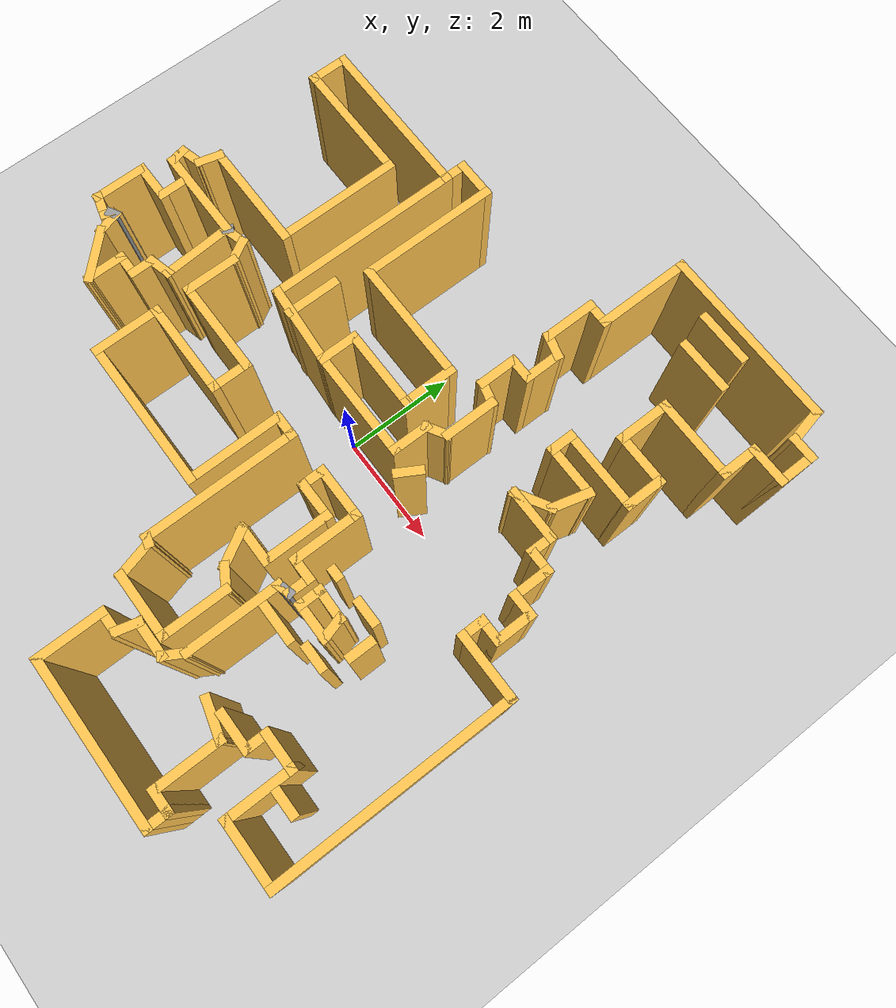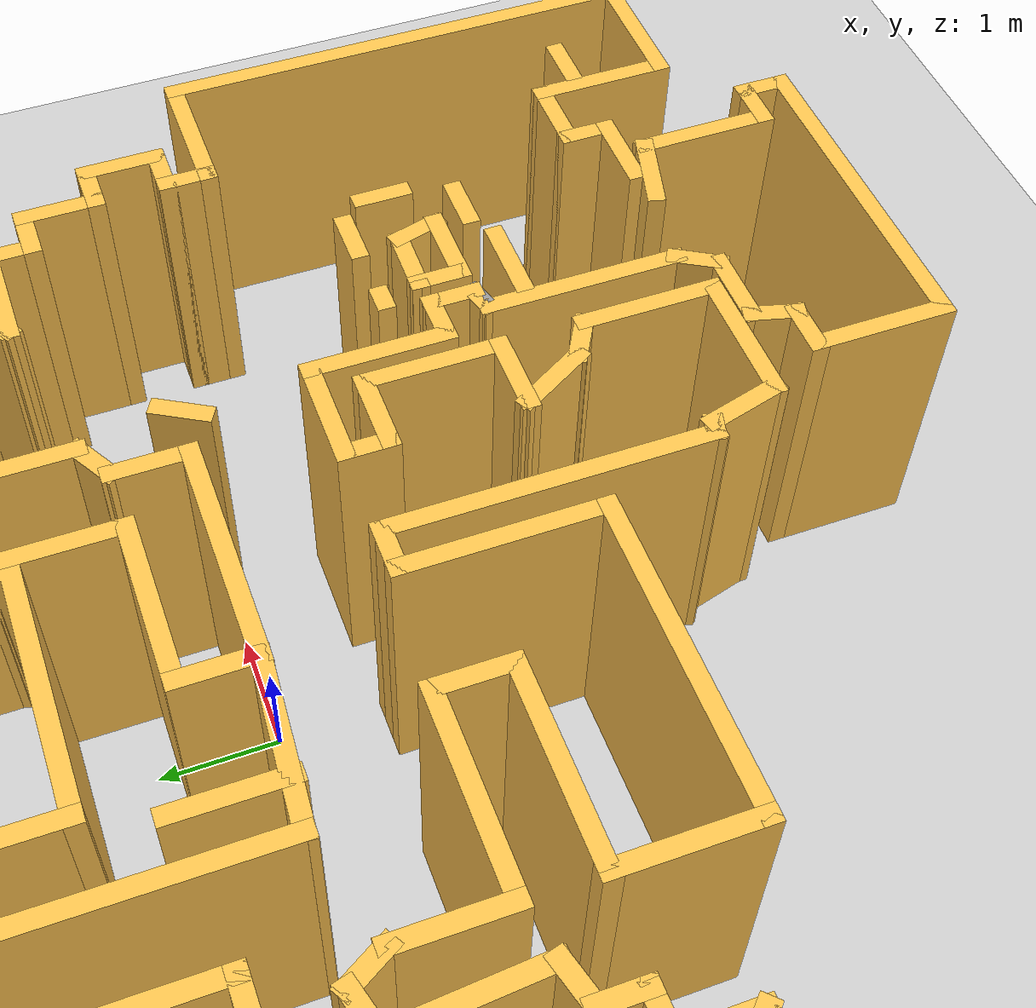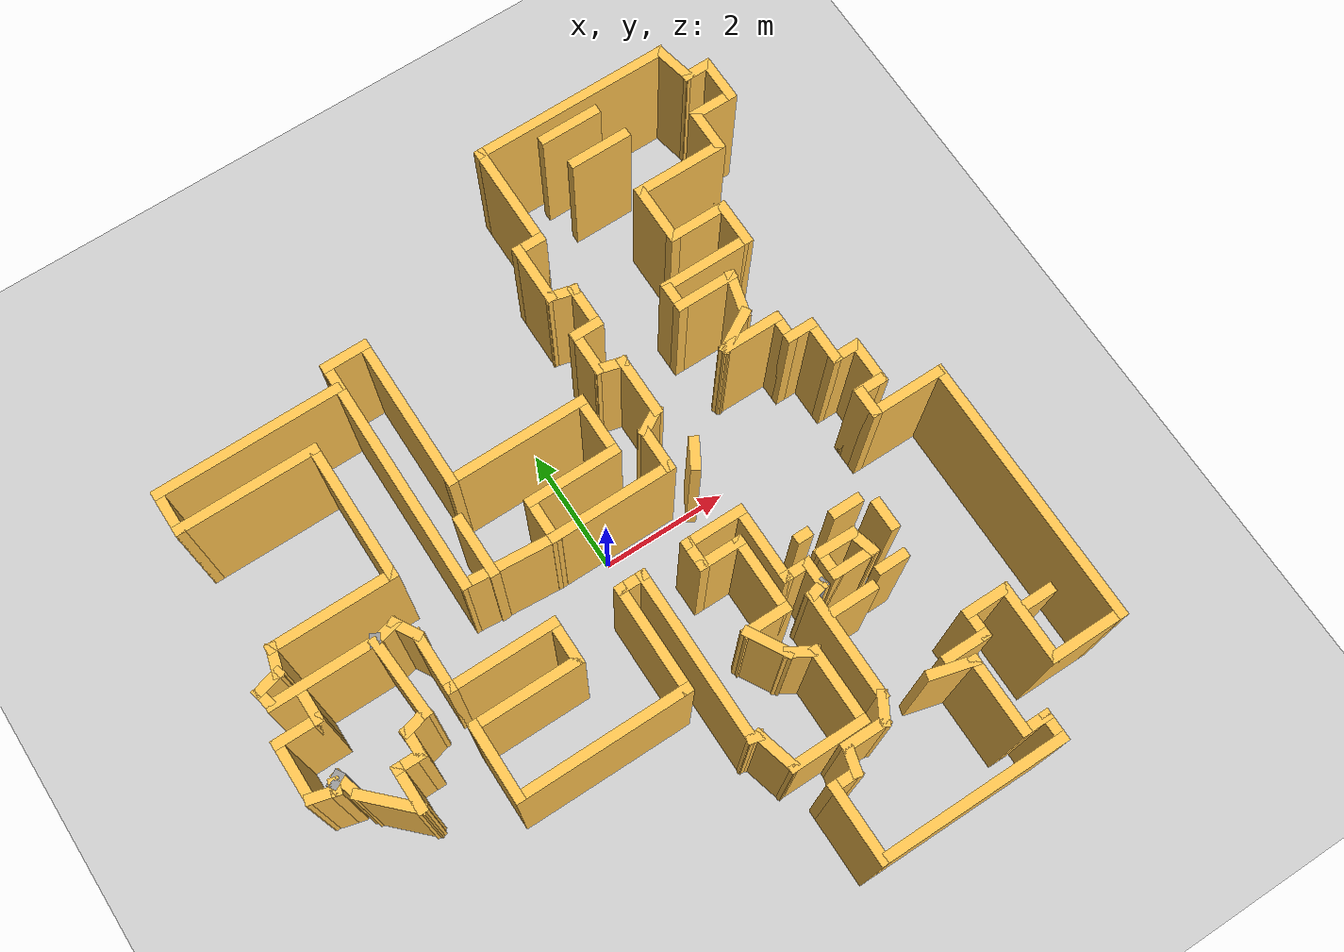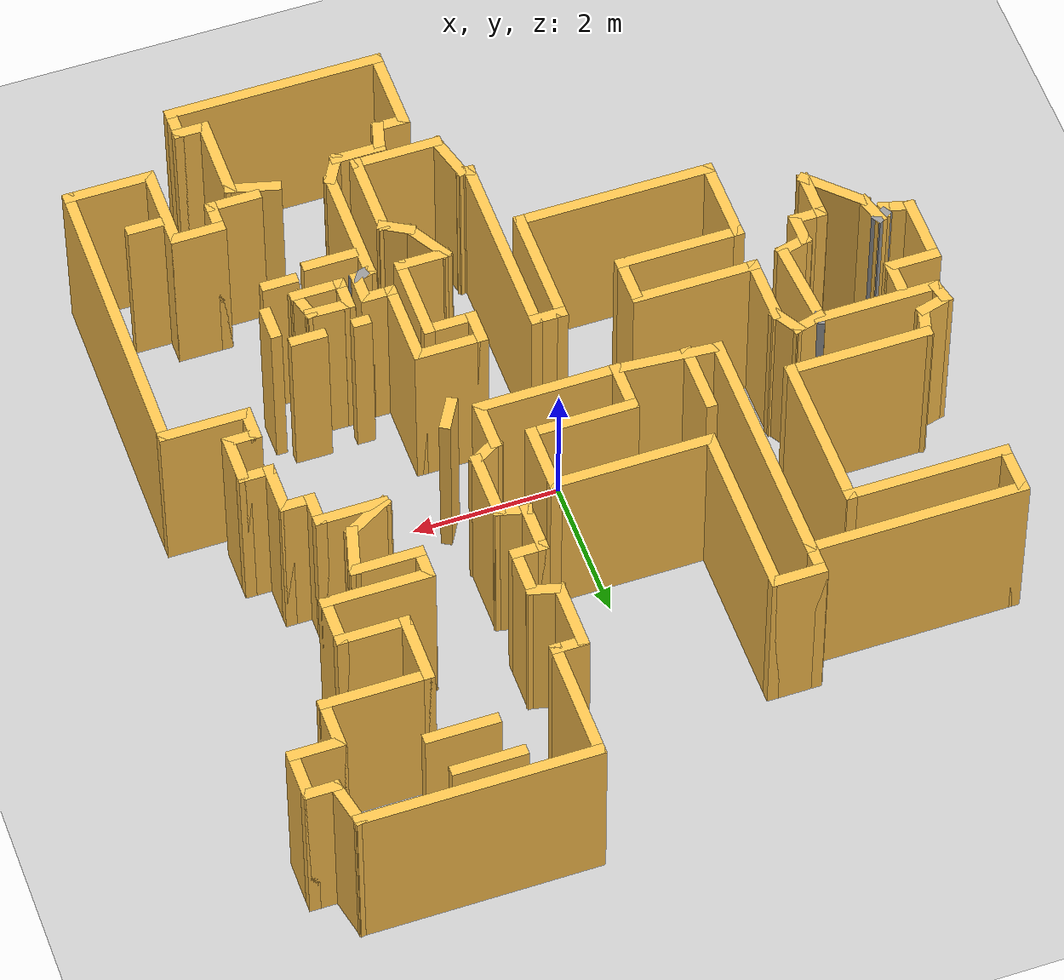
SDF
<sdf version="1.6">
 <world name="default">
  <light name="sun" type="directional">
   <pose>0 0 10 0 -0 0</pose>
   <diffuse>0.8 0.8 0.8 1</diffuse>
   <specular>0.2 0.2 0.2 1</specular>
   <attenuation>
    <range>1000</range>
    <constant>0.9</constant>
    <linear>0.01</linear>
    <quadratic>0.001</quadratic>
   </attenuation>
   <direction>-0.5 0.1 -0.9</direction>
  </light>
  <model name="ground_plane">
   <static>1</static>
   <link name="link">
    <collision name="collision">
     <geometry><plane><normal>0 0 1</normal><size>100 100</size></plane></geometry>
     <surface>
      <contact><collide_bitmask>65535</collide_bitmask></contact>
      <friction><ode><mu>100</mu><mu2>50</mu2></ode></friction>
     </surface>
    </collision>
    <visual name="visual">
     <cast_shadows>0</cast_shadows>
     <geometry><plane><normal>0 0 1</normal><size>100 100</size></plane></geometry>
     <material>
      <script><uri>file://media/materials/scripts/gazebo.material</uri><name>Gazebo/Grey</name></script>
     </material>
    </visual>
   </link>
  </model>
  <gravity>0 0 -9.8</gravity>
  <magnetic_field>6e-06 2.3e-05 -4.2e-05</magnetic_field>
  <atmosphere type="adiabatic"/>
  <physics name="default_physics" default="0" type="ode">
   <max_step_size>0.001</max_step_size>
   <real_time_factor>1</real_time_factor>
   <real_time_update_rate>1000</real_time_update_rate>
  </physics>
  <scene><ambient>0.4 0.4 0.4 1</ambient><background>0.7 0.7 0.7 1</background><shadows>1</shadows></scene>
  <audio><device>default</device></audio>
  <spherical_coordinates>
   <surface_model>EARTH_WGS84</surface_model>
   <latitude_deg>0</latitude_deg>
   <longitude_deg>0</longitude_deg>
   <elevation>0</elevation>
   <heading_deg>0</heading_deg>
  </spherical_coordinates>
  <model name="map_21">
   <pose>-0.097763 -0.060898 0 0 -0 0</pose>
   <link name="Wall_0">
    <collision name="Wall_0_Collision">
     <geometry><box><size>3.25 0.15 2.5</size></box></geometry>
     <pose>0 0 1.25 0 -0 0</pose>
    </collision>
    <visual name="Wall_0_Visual">
     <pose>0 0 1.25 0 -0 0</pose>
     <geometry><box><size>3.25 0.15 2.5</size></box></geometry>
     <material>
      <script><uri>file://media/materials/scripts/gazebo.material</uri><name>Gazebo/Grey</name></script>
      <ambient>1 0.764706 0.305882 1</ambient>
     </material>
     <meta><layer>0</layer></meta>
    </visual>
    <pose>3.10195 5.67023 0 0 -0 3.14159</pose>
   </link>
   <link name="Wall_1">
    <collision name="Wall_1_Collision">
     <geometry><box><size>1.75 0.15 2.5</size></box></geometry>
     <pose>0 0 1.25 0 -0 0</pose>
    </collision>
    <visual name="Wall_1_Visual">
     <pose>0 0 1.25 0 -0 0</pose>
     <geometry><box><size>1.75 0.15 2.5</size></box></geometry>
     <material>
      <script><uri>file://media/materials/scripts/gazebo.material</uri><name>Gazebo/Grey</name></script>
      <ambient>1 0.764706 0.305882 1</ambient>
     </material>
     <meta><layer>0</layer></meta>
    </visual>
    <pose>1.55195 4.87023 0 0 -0 -1.5708</pose>
   </link>
   <link name="Wall_10">
    <collision name="Wall_10_Collision">
     <geometry><box><size>0.5 0.15 2.5</size></box></geometry>
     <pose>0 0 1.25 0 -0 0</pose>
    </collision>
    <visual name="Wall_10_Visual">
     <pose>0 0 1.25 0 -0 0</pose>
     <geometry><box><size>0.5 0.15 2.5</size></box></geometry>
     <material>
      <script><uri>file://media/materials/scripts/gazebo.material</uri><name>Gazebo/Grey</name></script>
      <ambient>1 0.764706 0.305882 1</ambient>
     </material>
     <meta><layer>0</layer></meta>
    </visual>
    <pose>1.37654 0.901556 0 0 -0 -2.61799</pose>
   </link>
   <link name="Wall_102">
    <collision name="Wall_102_Collision">
     <geometry><box><size>3 0.15 2.5</size></box></geometry>
     <pose>0 0 1.25 0 -0 0</pose>
    </collision>
    <visual name="Wall_102_Visual">
     <pose>0 0 1.25 0 -0 0</pose>
     <geometry><box><size>3 0.15 2.5</size></box></geometry>
     <material>
      <script><uri>file://media/materials/scripts/gazebo.material</uri><name>Gazebo/Grey</name></script>
      <ambient>1 0.764706 0.305882 1</ambient>
     </material>
     <meta><layer>0</layer></meta>
    </visual>
    <pose>2.05029 -5.6843 0 0 -0 0</pose>
   </link>
   <link name="Wall_103">
    <collision name="Wall_103_Collision">
     <geometry><box><size>0.5 0.15 2.5</size></box></geometry>
     <pose>0 0 1.25 0 -0 0</pose>
    </collision>
    <visual name="Wall_103_Visual">
     <pose>0 0 1.25 0 -0 0</pose>
     <geometry><box><size>0.5 0.15 2.5</size></box></geometry>
     <material>
      <script><uri>file://media/materials/scripts/gazebo.material</uri><name>Gazebo/Grey</name></script>
      <ambient>1 0.764706 0.305882 1</ambient>
     </material>
     <meta><layer>0</layer></meta>
    </visual>
    <pose>3.47528 -5.5093 0 0 -0 1.5708</pose>
   </link>
   <link name="Wall_104">
    <collision name="Wall_104_Collision">
     <geometry><box><size>0.5 0.15 2.5</size></box></geometry>
     <pose>0 0 1.25 0 -0 0</pose>
    </collision>
    <visual name="Wall_104_Visual">
     <pose>0 0 1.25 0 -0 0</pose>
     <geometry><box><size>0.5 0.15 2.5</size></box></geometry>
     <material>
      <script><uri>file://media/materials/scripts/gazebo.material</uri><name>Gazebo/Grey</name></script>
      <ambient>1 0.764706 0.305882 1</ambient>
     </material>
     <meta><layer>0</layer></meta>
    </visual>
    <pose>3.30029 -5.3343 0 0 -0 3.14159</pose>
   </link>
   <link name="Wall_107">
    <collision name="Wall_107_Collision">
     <geometry><box><size>1.25 0.15 2.5</size></box></geometry>
     <pose>0 0 1.25 0 -0 0</pose>
    </collision>
    <visual name="Wall_107_Visual">
     <pose>0 0 1.25 0 -0 0</pose>
     <geometry><box><size>1.25 0.15 2.5</size></box></geometry>
     <material>
      <script><uri>file://media/materials/scripts/gazebo.material</uri><name>Gazebo/Grey</name></script>
      <ambient>1 0.764706 0.305882 1</ambient>
     </material>
     <meta><layer>0</layer></meta>
    </visual>
    <pose>3.12528 -4.7843 0 0 -0 1.5708</pose>
   </link>
   <link name="Wall_108">
    <collision name="Wall_108_Collision">
     <geometry><box><size>0.75 0.15 2.5</size></box></geometry>
     <pose>0 0 1.25 0 -0 0</pose>
    </collision>
    <visual name="Wall_108_Visual">
     <pose>0 0 1.25 0 -0 0</pose>
     <geometry><box><size>0.75 0.15 2.5</size></box></geometry>
     <material>
      <script><uri>file://media/materials/scripts/gazebo.material</uri><name>Gazebo/Grey</name></script>
      <ambient>1 0.764706 0.305882 1</ambient>
     </material>
     <meta><layer>0</layer></meta>
    </visual>
    <pose>2.83551 -4.15666 0 0 -0 2.87979</pose>
   </link>
   <link name="Wall_11">
    <collision name="Wall_11_Collision">
     <geometry><box><size>0.75 0.15 2.5</size></box></geometry>
     <pose>0 0 1.25 0 -0 0</pose>
    </collision>
    <visual name="Wall_11_Visual">
     <pose>0 0 1.25 0 -0 0</pose>
     <geometry><box><size>0.75 0.15 2.5</size></box></geometry>
     <material>
      <script><uri>file://media/materials/scripts/gazebo.material</uri><name>Gazebo/Grey</name></script>
      <ambient>1 0.764706 0.305882 1</ambient>
     </material>
     <meta><layer>0</layer></meta>
    </visual>
    <pose>1.22499 0.514056 0 0 -0 -1.5708</pose>
   </link>
   <link name="Wall_110">
    <collision name="Wall_110_Collision">
     <geometry><box><size>0.75 0.15 2.5</size></box></geometry>
     <pose>0 0 1.25 0 -0 0</pose>
    </collision>
    <visual name="Wall_110_Visual">
     <pose>0 0 1.25 0 -0 0</pose>
     <geometry><box><size>0.75 0.15 2.5</size></box></geometry>
     <material>
      <script><uri>file://media/materials/scripts/gazebo.material</uri><name>Gazebo/Grey</name></script>
      <ambient>1 0.764706 0.305882 1</ambient>
     </material>
     <meta><layer>0</layer></meta>
    </visual>
    <pose>3.14776 -4.0215 0 0 -0 0</pose>
   </link>
   <link name="Wall_114">
    <collision name="Wall_114_Collision">
     <geometry><box><size>0.5 0.15 2.5</size></box></geometry>
     <pose>0 0 1.25 0 -0 0</pose>
    </collision>
    <visual name="Wall_114_Visual">
     <pose>0 0 1.25 0 -0 0</pose>
     <geometry><box><size>0.5 0.15 2.5</size></box></geometry>
     <material>
      <script><uri>file://media/materials/scripts/gazebo.material</uri><name>Gazebo/Grey</name></script>
      <ambient>1 0.764706 0.305882 1</ambient>
     </material>
     <meta><layer>0</layer></meta>
    </visual>
    <pose>3.44776 -3.8465 0 0 -0 1.5708</pose>
   </link>
   <link name="Wall_115">
    <collision name="Wall_115_Collision">
     <geometry><box><size>0.75 0.15 2.5</size></box></geometry>
     <pose>0 0 1.25 0 -0 0</pose>
    </collision>
    <visual name="Wall_115_Visual">
     <pose>0 0 1.25 0 -0 0</pose>
     <geometry><box><size>0.75 0.15 2.5</size></box></geometry>
     <material>
      <script><uri>file://media/materials/scripts/gazebo.material</uri><name>Gazebo/Grey</name></script>
      <ambient>1 0.764706 0.305882 1</ambient>
     </material>
     <meta><layer>0</layer></meta>
    </visual>
    <pose>3.74776 -3.6715 0 0 -0 0</pose>
   </link>
   <link name="Wall_116">
    <collision name="Wall_116_Collision">
     <geometry><box><size>1.25 0.15 2.5</size></box></geometry>
     <pose>0 0 1.25 0 -0 0</pose>
    </collision>
    <visual name="Wall_116_Visual">
     <pose>0 0 1.25 0 -0 0</pose>
     <geometry><box><size>1.25 0.15 2.5</size></box></geometry>
     <material>
      <script><uri>file://media/materials/scripts/gazebo.material</uri><name>Gazebo/Grey</name></script>
      <ambient>1 0.764706 0.305882 1</ambient>
     </material>
     <meta><layer>0</layer></meta>
    </visual>
    <pose>4.04776 -4.2215 0 0 -0 -1.5708</pose>
   </link>
   <link name="Wall_117">
    <collision name="Wall_117_Collision">
     <geometry><box><size>1.25 0.15 2.5</size></box></geometry>
     <pose>0 0 1.25 0 -0 0</pose>
    </collision>
    <visual name="Wall_117_Visual">
     <pose>0 0 1.25 0 -0 0</pose>
     <geometry><box><size>1.25 0.15 2.5</size></box></geometry>
     <material>
      <script><uri>file://media/materials/scripts/gazebo.material</uri><name>Gazebo/Grey</name></script>
      <ambient>1 0.764706 0.305882 1</ambient>
     </material>
     <meta><layer>0</layer></meta>
    </visual>
    <pose>4.59776 -4.7715 0 0 -0 0</pose>
   </link>
   <link name="Wall_118">
    <collision name="Wall_118_Collision">
     <geometry><box><size>4.25 0.15 2.5</size></box></geometry>
     <pose>0 0 1.25 0 -0 0</pose>
    </collision>
    <visual name="Wall_118_Visual">
     <pose>0 0 1.25 0 -0 0</pose>
     <geometry><box><size>4.25 0.15 2.5</size></box></geometry>
     <material>
      <script><uri>file://media/materials/scripts/gazebo.material</uri><name>Gazebo/Grey</name></script>
      <ambient>1 0.764706 0.305882 1</ambient>
     </material>
     <meta><layer>0</layer></meta>
    </visual>
    <pose>5.14776 -2.7215 0 0 -0 1.5708</pose>
   </link>
   <link name="Wall_119">
    <collision name="Wall_119_Collision">
     <geometry><box><size>1.25 0.15 2.5</size></box></geometry>
     <pose>0 0 1.25 0 -0 0</pose>
    </collision>
    <visual name="Wall_119_Visual">
     <pose>0 0 1.25 0 -0 0</pose>
     <geometry><box><size>1.25 0.15 2.5</size></box></geometry>
     <material>
      <script><uri>file://media/materials/scripts/gazebo.material</uri><name>Gazebo/Grey</name></script>
      <ambient>1 0.764706 0.305882 1</ambient>
     </material>
     <meta><layer>0</layer></meta>
    </visual>
    <pose>4.59776 -0.671496 0 0 -0 3.14159</pose>
   </link>
   <link name="Wall_12">
    <collision name="Wall_12_Collision">
     <geometry><box><size>2 0.15 2.5</size></box></geometry>
     <pose>0 0 1.25 0 -0 0</pose>
    </collision>
    <visual name="Wall_12_Visual">
     <pose>0 0 1.25 0 -0 0</pose>
     <geometry><box><size>2 0.15 2.5</size></box></geometry>
     <material>
      <script><uri>file://media/materials/scripts/gazebo.material</uri><name>Gazebo/Grey</name></script>
      <ambient>1 0.764706 0.305882 1</ambient>
     </material>
     <meta><layer>0</layer></meta>
    </visual>
    <pose>0.299987 0.214056 0 0 -0 3.14159</pose>
   </link>
   <link name="Wall_122">
    <collision name="Wall_122_Collision">
     <geometry><box><size>0.5 0.15 2.5</size></box></geometry>
     <pose>0 0 1.25 0 -0 0</pose>
    </collision>
    <visual name="Wall_122_Visual">
     <pose>0 0 1.25 0 -0 0</pose>
     <geometry><box><size>0.5 0.15 2.5</size></box></geometry>
     <material>
      <script><uri>file://media/materials/scripts/gazebo.material</uri><name>Gazebo/Grey</name></script>
      <ambient>1 0.764706 0.305882 1</ambient>
     </material>
     <meta><layer>0</layer></meta>
    </visual>
    <pose>4.04776 -0.496496 0 0 -0 1.5708</pose>
   </link>
   <link name="Wall_123">
    <collision name="Wall_123_Collision">
     <geometry><box><size>0.5 0.15 2.5</size></box></geometry>
     <pose>0 0 1.25 0 -0 0</pose>
    </collision>
    <visual name="Wall_123_Visual">
     <pose>0 0 1.25 0 -0 0</pose>
     <geometry><box><size>0.5 0.15 2.5</size></box></geometry>
     <material>
      <script><uri>file://media/materials/scripts/gazebo.material</uri><name>Gazebo/Grey</name></script>
      <ambient>1 0.764706 0.305882 1</ambient>
     </material>
     <meta><layer>0</layer></meta>
    </visual>
    <pose>4.22276 -0.321496 0 0 -0 0</pose>
   </link>
   <link name="Wall_124">
    <collision name="Wall_124_Collision">
     <geometry><box><size>0.75 0.15 2.5</size></box></geometry>
     <pose>0 0 1.25 0 -0 0</pose>
    </collision>
    <visual name="Wall_124_Visual">
     <pose>0 0 1.25 0 -0 0</pose>
     <geometry><box><size>0.75 0.15 2.5</size></box></geometry>
     <material>
      <script><uri>file://media/materials/scripts/gazebo.material</uri><name>Gazebo/Grey</name></script>
      <ambient>1 0.764706 0.305882 1</ambient>
     </material>
     <meta><layer>0</layer></meta>
    </visual>
    <pose>4.39776 -0.021496 0 0 -0 1.5708</pose>
   </link>
   <link name="Wall_125">
    <collision name="Wall_125_Collision">
     <geometry><box><size>0.5 0.15 2.5</size></box></geometry>
     <pose>0 0 1.25 0 -0 0</pose>
    </collision>
    <visual name="Wall_125_Visual">
     <pose>0 0 1.25 0 -0 0</pose>
     <geometry><box><size>0.5 0.15 2.5</size></box></geometry>
     <material>
      <script><uri>file://media/materials/scripts/gazebo.material</uri><name>Gazebo/Grey</name></script>
      <ambient>1 0.764706 0.305882 1</ambient>
     </material>
     <meta><layer>0</layer></meta>
    </visual>
    <pose>4.22276 0.278504 0 0 -0 3.14159</pose>
   </link>
   <link name="Wall_126">
    <collision name="Wall_126_Collision">
     <geometry><box><size>0.75 0.15 2.5</size></box></geometry>
     <pose>0 0 1.25 0 -0 0</pose>
    </collision>
    <visual name="Wall_126_Visual">
     <pose>0 0 1.25 0 -0 0</pose>
     <geometry><box><size>0.75 0.15 2.5</size></box></geometry>
     <material>
      <script><uri>file://media/materials/scripts/gazebo.material</uri><name>Gazebo/Grey</name></script>
      <ambient>1 0.764706 0.305882 1</ambient>
     </material>
     <meta><layer>0</layer></meta>
    </visual>
    <pose>4.04776 0.578504 0 0 -0 1.5708</pose>
   </link>
   <link name="Wall_127">
    <collision name="Wall_127_Collision">
     <geometry><box><size>0.5 0.15 2.5</size></box></geometry>
     <pose>0 0 1.25 0 -0 0</pose>
    </collision>
    <visual name="Wall_127_Visual">
     <pose>0 0 1.25 0 -0 0</pose>
     <geometry><box><size>0.5 0.15 2.5</size></box></geometry>
     <material>
      <script><uri>file://media/materials/scripts/gazebo.material</uri><name>Gazebo/Grey</name></script>
      <ambient>1 0.764706 0.305882 1</ambient>
     </material>
     <meta><layer>0</layer></meta>
    </visual>
    <pose>3.87276 0.878504 0 0 -0 3.14159</pose>
   </link>
   <link name="Wall_128">
    <collision name="Wall_128_Collision">
     <geometry><box><size>0.5 0.15 2.5</size></box></geometry>
     <pose>0 0 1.25 0 -0 0</pose>
    </collision>
    <visual name="Wall_128_Visual">
     <pose>0 0 1.25 0 -0 0</pose>
     <geometry><box><size>0.5 0.15 2.5</size></box></geometry>
     <material>
      <script><uri>file://media/materials/scripts/gazebo.material</uri><name>Gazebo/Grey</name></script>
      <ambient>1 0.764706 0.305882 1</ambient>
     </material>
     <meta><layer>0</layer></meta>
    </visual>
    <pose>3.69776 1.0535 0 0 -0 1.5708</pose>
   </link>
   <link name="Wall_129">
    <collision name="Wall_129_Collision">
     <geometry><box><size>1 0.15 2.5</size></box></geometry>
     <pose>0 0 1.25 0 -0 0</pose>
    </collision>
    <visual name="Wall_129_Visual">
     <pose>0 0 1.25 0 -0 0</pose>
     <geometry><box><size>1 0.15 2.5</size></box></geometry>
     <material>
      <script><uri>file://media/materials/scripts/gazebo.material</uri><name>Gazebo/Grey</name></script>
      <ambient>1 0.764706 0.305882 1</ambient>
     </material>
     <meta><layer>0</layer></meta>
    </visual>
    <pose>3.27276 1.2285 0 0 -0 3.14159</pose>
   </link>
   <link name="Wall_13">
    <collision name="Wall_13_Collision">
     <geometry><box><size>0.75 0.15 2.5</size></box></geometry>
     <pose>0 0 1.25 0 -0 0</pose>
    </collision>
    <visual name="Wall_13_Visual">
     <pose>0 0 1.25 0 -0 0</pose>
     <geometry><box><size>0.75 0.15 2.5</size></box></geometry>
     <material>
      <script><uri>file://media/materials/scripts/gazebo.material</uri><name>Gazebo/Grey</name></script>
      <ambient>1 0.764706 0.305882 1</ambient>
     </material>
     <meta><layer>0</layer></meta>
    </visual>
    <pose>-0.625014 0.514056 0 0 -0 1.5708</pose>
   </link>
   <link name="Wall_130">
    <collision name="Wall_130_Collision">
     <geometry><box><size>0.75 0.15 2.5</size></box></geometry>
     <pose>0 0 1.25 0 -0 0</pose>
    </collision>
    <visual name="Wall_130_Visual">
     <pose>0 0 1.25 0 -0 0</pose>
     <geometry><box><size>0.75 0.15 2.5</size></box></geometry>
     <material>
      <script><uri>file://media/materials/scripts/gazebo.material</uri><name>Gazebo/Grey</name></script>
      <ambient>1 0.764706 0.305882 1</ambient>
     </material>
     <meta><layer>0</layer></meta>
    </visual>
    <pose>3.10757 1.3785 0 0 -0 0.523599</pose>
   </link>
   <link name="Wall_131">
    <collision name="Wall_131_Collision">
     <geometry><box><size>0.75 0.15 2.5</size></box></geometry>
     <pose>0 0 1.25 0 -0 0</pose>
    </collision>
    <visual name="Wall_131_Visual">
     <pose>0 0 1.25 0 -0 0</pose>
     <geometry><box><size>0.75 0.15 2.5</size></box></geometry>
     <material>
      <script><uri>file://media/materials/scripts/gazebo.material</uri><name>Gazebo/Grey</name></script>
      <ambient>1 0.764706 0.305882 1</ambient>
     </material>
     <meta><layer>0</layer></meta>
    </visual>
    <pose>3.44502 1.81828 0 0 -0 1.309</pose>
   </link>
   <link name="Wall_132">
    <collision name="Wall_132_Collision">
     <geometry><box><size>1 0.15 2.5</size></box></geometry>
     <pose>0 0 1.25 0 -0 0</pose>
    </collision>
    <visual name="Wall_132_Visual">
     <pose>0 0 1.25 0 -0 0</pose>
     <geometry><box><size>1 0.15 2.5</size></box></geometry>
     <material>
      <script><uri>file://media/materials/scripts/gazebo.material</uri><name>Gazebo/Grey</name></script>
      <ambient>1 0.764706 0.305882 1</ambient>
     </material>
     <meta><layer>0</layer></meta>
    </visual>
    <pose>3.09767 2.10806 0 0 -0 3.14159</pose>
   </link>
   <link name="Wall_133">
    <collision name="Wall_133_Collision">
     <geometry><box><size>0.5 0.15 2.5</size></box></geometry>
     <pose>0 0 1.25 0 -0 0</pose>
    </collision>
    <visual name="Wall_133_Visual">
     <pose>0 0 1.25 0 -0 0</pose>
     <geometry><box><size>0.5 0.15 2.5</size></box></geometry>
     <material>
      <script><uri>file://media/materials/scripts/gazebo.material</uri><name>Gazebo/Grey</name></script>
      <ambient>1 0.764706 0.305882 1</ambient>
     </material>
     <meta><layer>0</layer></meta>
    </visual>
    <pose>2.67267 2.28306 0 0 -0 1.5708</pose>
   </link>
   <link name="Wall_134">
    <collision name="Wall_134_Collision">
     <geometry><box><size>1.5 0.15 2.5</size></box></geometry>
     <pose>0 0 1.25 0 -0 0</pose>
    </collision>
    <visual name="Wall_134_Visual">
     <pose>0 0 1.25 0 -0 0</pose>
     <geometry><box><size>1.5 0.15 2.5</size></box></geometry>
     <material>
      <script><uri>file://media/materials/scripts/gazebo.material</uri><name>Gazebo/Grey</name></script>
      <ambient>1 0.764706 0.305882 1</ambient>
     </material>
     <meta><layer>0</layer></meta>
    </visual>
    <pose>3.34767 2.45806 0 0 -0 0</pose>
   </link>
   <link name="Wall_135">
    <collision name="Wall_135_Collision">
     <geometry><box><size>0.75 0.15 2.5</size></box></geometry>
     <pose>0 0 1.25 0 -0 0</pose>
    </collision>
    <visual name="Wall_135_Visual">
     <pose>0 0 1.25 0 -0 0</pose>
     <geometry><box><size>0.75 0.15 2.5</size></box></geometry>
     <material>
      <script><uri>file://media/materials/scripts/gazebo.material</uri><name>Gazebo/Grey</name></script>
      <ambient>1 0.764706 0.305882 1</ambient>
     </material>
     <meta><layer>0</layer></meta>
    </visual>
    <pose>4.02267 2.75806 0 0 -0 1.5708</pose>
   </link>
   <link name="Wall_136">
    <collision name="Wall_136_Collision">
     <geometry><box><size>1 0.15 2.5</size></box></geometry>
     <pose>0 0 1.25 0 -0 0</pose>
    </collision>
    <visual name="Wall_136_Visual">
     <pose>0 0 1.25 0 -0 0</pose>
     <geometry><box><size>1 0.15 2.5</size></box></geometry>
     <material>
      <script><uri>file://media/materials/scripts/gazebo.material</uri><name>Gazebo/Grey</name></script>
      <ambient>1 0.764706 0.305882 1</ambient>
     </material>
     <meta><layer>0</layer></meta>
    </visual>
    <pose>3.59767 3.05806 0 0 -0 3.14159</pose>
   </link>
   <link name="Wall_137">
    <collision name="Wall_137_Collision">
     <geometry><box><size>1 0.15 2.5</size></box></geometry>
     <pose>0 0 1.25 0 -0 0</pose>
    </collision>
    <visual name="Wall_137_Visual">
     <pose>0 0 1.25 0 -0 0</pose>
     <geometry><box><size>1 0.15 2.5</size></box></geometry>
     <material>
      <script><uri>file://media/materials/scripts/gazebo.material</uri><name>Gazebo/Grey</name></script>
      <ambient>1 0.764706 0.305882 1</ambient>
     </material>
     <meta><layer>0</layer></meta>
    </visual>
    <pose>3.17267 3.48306 0 0 -0 1.5708</pose>
   </link>
   <link name="Wall_138">
    <collision name="Wall_138_Collision">
     <geometry><box><size>1.5 0.15 2.5</size></box></geometry>
     <pose>0 0 1.25 0 -0 0</pose>
    </collision>
    <visual name="Wall_138_Visual">
     <pose>0 0 1.25 0 -0 0</pose>
     <geometry><box><size>1.5 0.15 2.5</size></box></geometry>
     <material>
      <script><uri>file://media/materials/scripts/gazebo.material</uri><name>Gazebo/Grey</name></script>
      <ambient>1 0.764706 0.305882 1</ambient>
     </material>
     <meta><layer>0</layer></meta>
    </visual>
    <pose>3.84767 3.90806 0 0 -0 0</pose>
   </link>
   <link name="Wall_139">
    <collision name="Wall_139_Collision">
     <geometry><box><size>0.75 0.15 2.5</size></box></geometry>
     <pose>0 0 1.25 0 -0 0</pose>
    </collision>
    <visual name="Wall_139_Visual">
     <pose>0 0 1.25 0 -0 0</pose>
     <geometry><box><size>0.75 0.15 2.5</size></box></geometry>
     <material>
      <script><uri>file://media/materials/scripts/gazebo.material</uri><name>Gazebo/Grey</name></script>
      <ambient>1 0.764706 0.305882 1</ambient>
     </material>
     <meta><layer>0</layer></meta>
    </visual>
    <pose>4.52267 4.20806 0 0 -0 1.5708</pose>
   </link>
   <link name="Wall_14">
    <collision name="Wall_14_Collision">
     <geometry><box><size>1.5 0.15 2.5</size></box></geometry>
     <pose>0 0 1.25 0 -0 0</pose>
    </collision>
    <visual name="Wall_14_Visual">
     <pose>0 0 1.25 0 -0 0</pose>
     <geometry><box><size>1.5 0.15 2.5</size></box></geometry>
     <material>
      <script><uri>file://media/materials/scripts/gazebo.material</uri><name>Gazebo/Grey</name></script>
      <ambient>1 0.764706 0.305882 1</ambient>
     </material>
     <meta><layer>0</layer></meta>
    </visual>
    <pose>0.049987 0.814056 0 0 -0 0</pose>
   </link>
   <link name="Wall_140">
    <collision name="Wall_140_Collision">
     <geometry><box><size>0.75 0.15 2.5</size></box></geometry>
     <pose>0 0 1.25 0 -0 0</pose>
    </collision>
    <visual name="Wall_140_Visual">
     <pose>0 0 1.25 0 -0 0</pose>
     <geometry><box><size>0.75 0.15 2.5</size></box></geometry>
     <material>
      <script><uri>file://media/materials/scripts/gazebo.material</uri><name>Gazebo/Grey</name></script>
      <ambient>1 0.764706 0.305882 1</ambient>
     </material>
     <meta><layer>0</layer></meta>
    </visual>
    <pose>4.82267 4.50806 0 0 -0 0</pose>
   </link>
   <link name="Wall_141">
    <collision name="Wall_141_Collision">
     <geometry><box><size>0.75 0.15 2.5</size></box></geometry>
     <pose>0 0 1.25 0 -0 0</pose>
    </collision>
    <visual name="Wall_141_Visual">
     <pose>0 0 1.25 0 -0 0</pose>
     <geometry><box><size>0.75 0.15 2.5</size></box></geometry>
     <material>
      <script><uri>file://media/materials/scripts/gazebo.material</uri><name>Gazebo/Grey</name></script>
      <ambient>1 0.764706 0.305882 1</ambient>
     </material>
     <meta><layer>0</layer></meta>
    </visual>
    <pose>5.12267 4.80806 0 0 -0 1.5708</pose>
   </link>
   <link name="Wall_142">
    <collision name="Wall_142_Collision">
     <geometry><box><size>0.5 0.15 2.5</size></box></geometry>
     <pose>0 0 1.25 0 -0 0</pose>
    </collision>
    <visual name="Wall_142_Visual">
     <pose>0 0 1.25 0 -0 0</pose>
     <geometry><box><size>0.5 0.15 2.5</size></box></geometry>
     <material>
      <script><uri>file://media/materials/scripts/gazebo.material</uri><name>Gazebo/Grey</name></script>
      <ambient>1 0.764706 0.305882 1</ambient>
     </material>
     <meta><layer>0</layer></meta>
    </visual>
    <pose>4.94767 5.10806 0 0 -0 3.14159</pose>
   </link>
   <link name="Wall_143">
    <collision name="Wall_143_Collision">
     <geometry><box><size>0.724985 0.15 2.5</size></box></geometry>
     <pose>0 0 1.25 0 -0 0</pose>
    </collision>
    <visual name="Wall_143_Visual">
     <pose>0 0 1.25 0 -0 0</pose>
     <geometry><box><size>0.724985 0.15 2.5</size></box></geometry>
     <material>
      <script><uri>file://media/materials/scripts/gazebo.material</uri><name>Gazebo/Grey</name></script>
      <ambient>1 0.764706 0.305882 1</ambient>
     </material>
     <meta><layer>0</layer></meta>
    </visual>
    <pose>4.71231 5.38914 0 0 -0 1.78232</pose>
   </link>
   <link name="Wall_145">
    <collision name="Wall_145_Collision">
     <geometry><box><size>1 0.15 2.5</size></box></geometry>
     <pose>0 0 1.25 0 -0 0</pose>
    </collision>
    <visual name="Wall_145_Visual">
     <pose>0 0 1.25 0 -0 0</pose>
     <geometry><box><size>1 0.15 2.5</size></box></geometry>
     <material>
      <script><uri>file://media/materials/scripts/gazebo.material</uri><name>Gazebo/Grey</name></script>
      <ambient>1 0.764706 0.305882 1</ambient>
     </material>
     <meta><layer>0</layer></meta>
    </visual>
    <pose>2.87954 5.36953 0 0 -0 0</pose>
   </link>
   <link name="Wall_147">
    <collision name="Wall_147_Collision">
     <geometry><box><size>1 0.15 2.5</size></box></geometry>
     <pose>0 0 1.25 0 -0 0</pose>
    </collision>
    <visual name="Wall_147_Visual">
     <pose>0 0 1.25 0 -0 0</pose>
     <geometry><box><size>1 0.15 2.5</size></box></geometry>
     <material>
      <script><uri>file://media/materials/scripts/gazebo.material</uri><name>Gazebo/Grey</name></script>
      <ambient>1 0.764706 0.305882 1</ambient>
     </material>
     <meta><layer>0</layer></meta>
    </visual>
    <pose>3.04145 4.8144 0 0 -0 0</pose>
   </link>
   <link name="Wall_15">
    <collision name="Wall_15_Collision">
     <geometry><box><size>1 0.15 2.5</size></box></geometry>
     <pose>0 0 1.25 0 -0 0</pose>
    </collision>
    <visual name="Wall_15_Visual">
     <pose>0 0 1.25 0 -0 0</pose>
     <geometry><box><size>1 0.15 2.5</size></box></geometry>
     <material>
      <script><uri>file://media/materials/scripts/gazebo.material</uri><name>Gazebo/Grey</name></script>
      <ambient>1 0.764706 0.305882 1</ambient>
     </material>
     <meta><layer>0</layer></meta>
    </visual>
    <pose>0.724986 1.23906 0 0 -0 1.5708</pose>
   </link>
   <link name="Wall_150">
    <collision name="Wall_150_Collision">
     <geometry><box><size>0.5 0.15 2.5</size></box></geometry>
     <pose>0 0 1.25 0 -0 0</pose>
    </collision>
    <visual name="Wall_150_Visual">
     <pose>0 0 1.25 0 -0 0</pose>
     <geometry><box><size>0.5 0.15 2.5</size></box></geometry>
     <material>
      <script><uri>file://media/materials/scripts/gazebo.material</uri><name>Gazebo/Grey</name></script>
      <ambient>1 0.764706 0.305882 1</ambient>
     </material>
     <meta><layer>0</layer></meta>
    </visual>
    <pose>1.62686 0.175504 0 0 -0 -2.0944</pose>
   </link>
   <link name="Wall_155">
    <collision name="Wall_155_Collision">
     <geometry><box><size>3.5 0.15 2.5</size></box></geometry>
     <pose>0 0 1.25 0 -0 0</pose>
    </collision>
    <visual name="Wall_155_Visual">
     <pose>0 0 1.25 0 -0 0</pose>
     <geometry><box><size>3.5 0.15 2.5</size></box></geometry>
     <material>
      <script><uri>file://media/materials/scripts/gazebo.material</uri><name>Gazebo/Grey</name></script>
      <ambient>1 0.764706 0.305882 1</ambient>
     </material>
     <meta><layer>0</layer></meta>
    </visual>
    <pose>-1.97501 1.98906 0 0 -0 -1.5708</pose>
   </link>
   <link name="Wall_156">
    <collision name="Wall_156_Collision">
     <geometry><box><size>1.5037 0.15 2.5</size></box></geometry>
     <pose>0 0 1.25 0 -0 0</pose>
    </collision>
    <visual name="Wall_156_Visual">
     <pose>0 0 1.25 0 -0 0</pose>
     <geometry><box><size>1.5037 0.15 2.5</size></box></geometry>
     <material>
      <script><uri>file://media/materials/scripts/gazebo.material</uri><name>Gazebo/Grey</name></script>
      <ambient>1 0.764706 0.305882 1</ambient>
     </material>
     <meta><layer>0</layer></meta>
    </visual>
    <pose>-1.30001 0.264056 0 0 -0 -0.073939</pose>
   </link>
   <link name="Wall_158">
    <collision name="Wall_158_Collision">
     <geometry><box><size>1 0.15 2.5</size></box></geometry>
     <pose>0 0 1.25 0 -0 0</pose>
    </collision>
    <visual name="Wall_158_Visual">
     <pose>0 0 1.25 0 -0 0</pose>
     <geometry><box><size>1 0.15 2.5</size></box></geometry>
     <material>
      <script><uri>file://media/materials/scripts/gazebo.material</uri><name>Gazebo/Grey</name></script>
      <ambient>1 0.764706 0.305882 1</ambient>
     </material>
     <meta><layer>0</layer></meta>
    </visual>
    <pose>-1.57019 0.688499 0 0 -0 -1.5708</pose>
   </link>
   <link name="Wall_16">
    <collision name="Wall_16_Collision">
     <geometry><box><size>2.25 0.15 2.5</size></box></geometry>
     <pose>0 0 1.25 0 -0 0</pose>
    </collision>
    <visual name="Wall_16_Visual">
     <pose>0 0 1.25 0 -0 0</pose>
     <geometry><box><size>2.25 0.15 2.5</size></box></geometry>
     <material>
      <script><uri>file://media/materials/scripts/gazebo.material</uri><name>Gazebo/Grey</name></script>
      <ambient>1 0.764706 0.305882 1</ambient>
     </material>
     <meta><layer>0</layer></meta>
    </visual>
    <pose>-0.325013 1.66406 0 0 -0 3.14159</pose>
   </link>
   <link name="Wall_161">
    <collision name="Wall_161_Collision">
     <geometry><box><size>0.75 0.15 2.5</size></box></geometry>
     <pose>0 0 1.25 0 -0 0</pose>
    </collision>
    <visual name="Wall_161_Visual">
     <pose>0 0 1.25 0 -0 0</pose>
     <geometry><box><size>0.75 0.15 2.5</size></box></geometry>
     <material>
      <script><uri>file://media/materials/scripts/gazebo.material</uri><name>Gazebo/Grey</name></script>
      <ambient>1 0.764706 0.305882 1</ambient>
     </material>
     <meta><layer>0</layer></meta>
    </visual>
    <pose>2.2688 -2.67992 0 0 -0 0</pose>
   </link>
   <link name="Wall_163">
    <collision name="Wall_163_Collision">
     <geometry><box><size>0.5 0.15 2.5</size></box></geometry>
     <pose>0 0 1.25 0 -0 0</pose>
    </collision>
    <visual name="Wall_163_Visual">
     <pose>0 0 1.25 0 -0 0</pose>
     <geometry><box><size>0.5 0.15 2.5</size></box></geometry>
     <material>
      <script><uri>file://media/materials/scripts/gazebo.material</uri><name>Gazebo/Grey</name></script>
      <ambient>1 0.764706 0.305882 1</ambient>
     </material>
     <meta><layer>0</layer></meta>
    </visual>
    <pose>2.99963 -2.54114 0 0 -0 0</pose>
   </link>
   <link name="Wall_165">
    <collision name="Wall_165_Collision">
     <geometry><box><size>0.5 0.15 2.5</size></box></geometry>
     <pose>0 0 1.25 0 -0 0</pose>
    </collision>
    <visual name="Wall_165_Visual">
     <pose>0 0 1.25 0 -0 0</pose>
     <geometry><box><size>0.5 0.15 2.5</size></box></geometry>
     <material>
      <script><uri>file://media/materials/scripts/gazebo.material</uri><name>Gazebo/Grey</name></script>
      <ambient>1 0.764706 0.305882 1</ambient>
     </material>
     <meta><layer>0</layer></meta>
    </visual>
    <pose>3.31037 -1.95283 0 0 -0 -1.5708</pose>
   </link>
   <link name="Wall_167">
    <collision name="Wall_167_Collision">
     <geometry><box><size>0.5 0.15 2.5</size></box></geometry>
     <pose>0 0 1.25 0 -0 0</pose>
    </collision>
    <visual name="Wall_167_Visual">
     <pose>0 0 1.25 0 -0 0</pose>
     <geometry><box><size>0.5 0.15 2.5</size></box></geometry>
     <material>
      <script><uri>file://media/materials/scripts/gazebo.material</uri><name>Gazebo/Grey</name></script>
      <ambient>1 0.764706 0.305882 1</ambient>
     </material>
     <meta><layer>0</layer></meta>
    </visual>
    <pose>2.26949 -2.09161 0 0 -0 -1.5708</pose>
   </link>
   <link name="Wall_17">
    <collision name="Wall_17_Collision">
     <geometry><box><size>2.5 0.15 2.5</size></box></geometry>
     <pose>0 0 1.25 0 -0 0</pose>
    </collision>
    <visual name="Wall_17_Visual">
     <pose>0 0 1.25 0 -0 0</pose>
     <geometry><box><size>2.5 0.15 2.5</size></box></geometry>
     <material>
      <script><uri>file://media/materials/scripts/gazebo.material</uri><name>Gazebo/Grey</name></script>
      <ambient>1 0.764706 0.305882 1</ambient>
     </material>
     <meta><layer>0</layer></meta>
    </visual>
    <pose>-1.37501 2.83906 0 0 -0 1.5708</pose>
   </link>
   <link name="Wall_172">
    <collision name="Wall_172_Collision">
     <geometry><box><size>0.75 0.15 2.5</size></box></geometry>
     <pose>0 0 1.25 0 -0 0</pose>
    </collision>
    <visual name="Wall_172_Visual">
     <pose>0 0 1.25 0 -0 0</pose>
     <geometry><box><size>0.75 0.15 2.5</size></box></geometry>
     <material>
      <script><uri>file://media/materials/scripts/gazebo.material</uri><name>Gazebo/Grey</name></script>
      <ambient>1 0.764706 0.305882 1</ambient>
     </material>
     <meta><layer>0</layer></meta>
    </visual>
    <pose>2.56949 -2.26661 0 0 -0 0</pose>
   </link>
   <link name="Wall_173">
    <collision name="Wall_173_Collision">
     <geometry><box><size>0.5 0.15 2.5</size></box></geometry>
     <pose>0 0 1.25 0 -0 0</pose>
    </collision>
    <visual name="Wall_173_Visual">
     <pose>0 0 1.25 0 -0 0</pose>
     <geometry><box><size>0.5 0.15 2.5</size></box></geometry>
     <material>
      <script><uri>file://media/materials/scripts/gazebo.material</uri><name>Gazebo/Grey</name></script>
      <ambient>1 0.764706 0.305882 1</ambient>
     </material>
     <meta><layer>0</layer></meta>
    </visual>
    <pose>2.8242 -2.09757 0 0 -0 1.8326</pose>
   </link>
   <link name="Wall_174">
    <collision name="Wall_174_Collision">
     <geometry><box><size>0.659553 0.15 2.5</size></box></geometry>
     <pose>0 0 1.25 0 -0 0</pose>
    </collision>
    <visual name="Wall_174_Visual">
     <pose>0 0 1.25 0 -0 0</pose>
     <geometry><box><size>0.659553 0.15 2.5</size></box></geometry>
     <material>
      <script><uri>file://media/materials/scripts/gazebo.material</uri><name>Gazebo/Grey</name></script>
      <ambient>1 0.764706 0.305882 1</ambient>
     </material>
     <meta><layer>0</layer></meta>
    </visual>
    <pose>2.5242 -1.92257 0 0 -0 3.11819</pose>
   </link>
   <link name="Wall_176">
    <collision name="Wall_176_Collision">
     <geometry><box><size>0.25 0.15 2.5</size></box></geometry>
     <pose>0 0 1.25 0 -0 0</pose>
    </collision>
    <visual name="Wall_176_Visual">
     <pose>0 0 1.25 0 -0 0</pose>
     <geometry><box><size>0.25 0.15 2.5</size></box></geometry>
     <material>
      <script><uri>file://media/materials/scripts/gazebo.material</uri><name>Gazebo/Grey</name></script>
      <ambient>1 0.764706 0.305882 1</ambient>
     </material>
     <meta><layer>0</layer></meta>
    </visual>
    <pose>2.20384 -1.59278 0 0 -0 0</pose>
   </link>
   <link name="Wall_178">
    <collision name="Wall_178_Collision">
     <geometry><box><size>0.5 0.15 2.5</size></box></geometry>
     <pose>0 0 1.25 0 -0 0</pose>
    </collision>
    <visual name="Wall_178_Visual">
     <pose>0 0 1.25 0 -0 0</pose>
     <geometry><box><size>0.5 0.15 2.5</size></box></geometry>
     <material>
      <script><uri>file://media/materials/scripts/gazebo.material</uri><name>Gazebo/Grey</name></script>
      <ambient>1 0.764706 0.305882 1</ambient>
     </material>
     <meta><layer>0</layer></meta>
    </visual>
    <pose>2.93024 -1.56965 0 0 -0 0</pose>
   </link>
   <link name="Wall_18">
    <collision name="Wall_18_Collision">
     <geometry><box><size>0.75 0.15 2.5</size></box></geometry>
     <pose>0 0 1.25 0 -0 0</pose>
    </collision>
    <visual name="Wall_18_Visual">
     <pose>0 0 1.25 0 -0 0</pose>
     <geometry><box><size>0.75 0.15 2.5</size></box></geometry>
     <material>
      <script><uri>file://media/materials/scripts/gazebo.material</uri><name>Gazebo/Grey</name></script>
      <ambient>1 0.764706 0.305882 1</ambient>
     </material>
     <meta><layer>0</layer></meta>
    </visual>
    <pose>-1.67501 4.01406 0 0 -0 3.14159</pose>
   </link>
   <link name="Wall_181">
    <collision name="Wall_181_Collision">
     <geometry><box><size>0.5 0.15 2.5</size></box></geometry>
     <pose>0 0 1.25 0 -0 0</pose>
    </collision>
    <visual name="Wall_181_Visual">
     <pose>0 0 1.25 0 -0 0</pose>
     <geometry><box><size>0.5 0.15 2.5</size></box></geometry>
     <material>
      <script><uri>file://media/materials/scripts/gazebo.material</uri><name>Gazebo/Grey</name></script>
      <ambient>1 0.764706 0.305882 1</ambient>
     </material>
     <meta><layer>0</layer></meta>
    </visual>
    <pose>4.36129 -3.99837 0 0 -0 3.14159</pose>
   </link>
   <link name="Wall_19">
    <collision name="Wall_19_Collision">
     <geometry><box><size>0.5 0.15 2.5</size></box></geometry>
     <pose>0 0 1.25 0 -0 0</pose>
    </collision>
    <visual name="Wall_19_Visual">
     <pose>0 0 1.25 0 -0 0</pose>
     <geometry><box><size>0.5 0.15 2.5</size></box></geometry>
     <material>
      <script><uri>file://media/materials/scripts/gazebo.material</uri><name>Gazebo/Grey</name></script>
      <ambient>1 0.764706 0.305882 1</ambient>
     </material>
     <meta><layer>0</layer></meta>
    </visual>
    <pose>-1.97501 3.83906 0 0 -0 -1.5708</pose>
   </link>
   <link name="Wall_2">
    <collision name="Wall_2_Collision">
     <geometry><box><size>0.5 0.15 2.5</size></box></geometry>
     <pose>0 0 1.25 0 -0 0</pose>
    </collision>
    <visual name="Wall_2_Visual">
     <pose>0 0 1.25 0 -0 0</pose>
     <geometry><box><size>0.5 0.15 2.5</size></box></geometry>
     <material>
      <script><uri>file://media/materials/scripts/gazebo.material</uri><name>Gazebo/Grey</name></script>
      <ambient>1 0.764706 0.305882 1</ambient>
     </material>
     <meta><layer>0</layer></meta>
    </visual>
    <pose>1.37695 4.07023 0 0 -0 3.14159</pose>
   </link>
   <link name="Wall_20">
    <collision name="Wall_20_Collision">
     <geometry><box><size>3 0.15 2.5</size></box></geometry>
     <pose>0 0 1.25 0 -0 0</pose>
    </collision>
    <visual name="Wall_20_Visual">
     <pose>0 0 1.25 0 -0 0</pose>
     <geometry><box><size>3 0.15 2.5</size></box></geometry>
     <material>
      <script><uri>file://media/materials/scripts/gazebo.material</uri><name>Gazebo/Grey</name></script>
      <ambient>1 0.764706 0.305882 1</ambient>
     </material>
     <meta><layer>0</layer></meta>
    </visual>
    <pose>-3.40001 3.66406 0 0 -0 3.14159</pose>
   </link>
   <link name="Wall_21">
    <collision name="Wall_21_Collision">
     <geometry><box><size>0.75 0.15 2.5</size></box></geometry>
     <pose>0 0 1.25 0 -0 0</pose>
    </collision>
    <visual name="Wall_21_Visual">
     <pose>0 0 1.25 0 -0 0</pose>
     <geometry><box><size>0.75 0.15 2.5</size></box></geometry>
     <material>
      <script><uri>file://media/materials/scripts/gazebo.material</uri><name>Gazebo/Grey</name></script>
      <ambient>1 0.764706 0.305882 1</ambient>
     </material>
     <meta><layer>0</layer></meta>
    </visual>
    <pose>-4.82501 3.36406 0 0 -0 -1.5708</pose>
   </link>
   <link name="Wall_22">
    <collision name="Wall_22_Collision">
     <geometry><box><size>2.25 0.15 2.5</size></box></geometry>
     <pose>0 0 1.25 0 -0 0</pose>
    </collision>
    <visual name="Wall_22_Visual">
     <pose>0 0 1.25 0 -0 0</pose>
     <geometry><box><size>2.25 0.15 2.5</size></box></geometry>
     <material>
      <script><uri>file://media/materials/scripts/gazebo.material</uri><name>Gazebo/Grey</name></script>
      <ambient>1 0.764706 0.305882 1</ambient>
     </material>
     <meta><layer>0</layer></meta>
    </visual>
    <pose>-3.77501 3.06406 0 0 -0 0</pose>
   </link>
   <link name="Wall_23">
    <collision name="Wall_23_Collision">
     <geometry><box><size>2.25 0.15 2.5</size></box></geometry>
     <pose>0 0 1.25 0 -0 0</pose>
    </collision>
    <visual name="Wall_23_Visual">
     <pose>0 0 1.25 0 -0 0</pose>
     <geometry><box><size>2.25 0.15 2.5</size></box></geometry>
     <material>
      <script><uri>file://media/materials/scripts/gazebo.material</uri><name>Gazebo/Grey</name></script>
      <ambient>1 0.764706 0.305882 1</ambient>
     </material>
     <meta><layer>0</layer></meta>
    </visual>
    <pose>-2.72501 2.01406 0 0 -0 -1.5708</pose>
   </link>
   <link name="Wall_24">
    <collision name="Wall_24_Collision">
     <geometry><box><size>2 0.15 2.5</size></box></geometry>
     <pose>0 0 1.25 0 -0 0</pose>
    </collision>
    <visual name="Wall_24_Visual">
     <pose>0 0 1.25 0 -0 0</pose>
     <geometry><box><size>2 0.15 2.5</size></box></geometry>
     <material>
      <script><uri>file://media/materials/scripts/gazebo.material</uri><name>Gazebo/Grey</name></script>
      <ambient>1 0.764706 0.305882 1</ambient>
     </material>
     <meta><layer>0</layer></meta>
    </visual>
    <pose>-3.65001 0.964056 0 0 -0 3.14159</pose>
   </link>
   <link name="Wall_29">
    <collision name="Wall_29_Collision">
     <geometry><box><size>0.5 0.15 2.5</size></box></geometry>
     <pose>0 0 1.25 0 -0 0</pose>
    </collision>
    <visual name="Wall_29_Visual">
     <pose>0 0 1.25 0 -0 0</pose>
     <geometry><box><size>0.5 0.15 2.5</size></box></geometry>
     <material>
      <script><uri>file://media/materials/scripts/gazebo.material</uri><name>Gazebo/Grey</name></script>
      <ambient>1 0.764706 0.305882 1</ambient>
     </material>
     <meta><layer>0</layer></meta>
    </visual>
    <pose>-4.62031 0.795019 0 0 -0 -1.8326</pose>
   </link>
   <link name="Wall_3">
    <collision name="Wall_3_Collision">
     <geometry><box><size>1 0.15 2.5</size></box></geometry>
     <pose>0 0 1.25 0 -0 0</pose>
    </collision>
    <visual name="Wall_3_Visual">
     <pose>0 0 1.25 0 -0 0</pose>
     <geometry><box><size>1 0.15 2.5</size></box></geometry>
     <material>
      <script><uri>file://media/materials/scripts/gazebo.material</uri><name>Gazebo/Grey</name></script>
      <ambient>1 0.764706 0.305882 1</ambient>
     </material>
     <meta><layer>0</layer></meta>
    </visual>
    <pose>1.20195 3.64523 0 0 -0 -1.5708</pose>
   </link>
   <link name="Wall_30">
    <collision name="Wall_30_Collision">
     <geometry><box><size>0.5 0.15 2.5</size></box></geometry>
     <pose>0 0 1.25 0 -0 0</pose>
    </collision>
    <visual name="Wall_30_Visual">
     <pose>0 0 1.25 0 -0 0</pose>
     <geometry><box><size>0.5 0.15 2.5</size></box></geometry>
     <material>
      <script><uri>file://media/materials/scripts/gazebo.material</uri><name>Gazebo/Grey</name></script>
      <ambient>1 0.764706 0.305882 1</ambient>
     </material>
     <meta><layer>0</layer></meta>
    </visual>
    <pose>-4.83464 0.580688 0 0 -0 -2.87979</pose>
   </link>
   <link name="Wall_35">
    <collision name="Wall_35_Collision">
     <geometry><box><size>0.366223 0.15 2.5</size></box></geometry>
     <pose>0 0 1.25 0 -0 0</pose>
    </collision>
    <visual name="Wall_35_Visual">
     <pose>0 0 1.25 0 -0 0</pose>
     <geometry><box><size>0.366223 0.15 2.5</size></box></geometry>
     <material>
      <script><uri>file://media/materials/scripts/gazebo.material</uri><name>Gazebo/Grey</name></script>
      <ambient>1 0.764706 0.305882 1</ambient>
     </material>
     <meta><layer>0</layer></meta>
    </visual>
    <pose>-4.98054 0.429787 0 0 -0 -1.35518</pose>
   </link>
   <link name="Wall_36">
    <collision name="Wall_36_Collision">
     <geometry><box><size>1.75 0.15 2.5</size></box></geometry>
     <pose>0 0 1.25 0 -0 0</pose>
    </collision>
    <visual name="Wall_36_Visual">
     <pose>0 0 1.25 0 -0 0</pose>
     <geometry><box><size>1.75 0.15 2.5</size></box></geometry>
     <material>
      <script><uri>file://media/materials/scripts/gazebo.material</uri><name>Gazebo/Grey</name></script>
      <ambient>1 0.764706 0.305882 1</ambient>
     </material>
     <meta><layer>0</layer></meta>
    </visual>
    <pose>-4.15741 0.301048 0 0 -0 0</pose>
   </link>
   <link name="Wall_37">
    <collision name="Wall_37_Collision">
     <geometry><box><size>0.196855 0.15 2.5</size></box></geometry>
     <pose>0 0 1.25 0 -0 0</pose>
    </collision>
    <visual name="Wall_37_Visual">
     <pose>0 0 1.25 0 -0 0</pose>
     <geometry><box><size>0.196855 0.15 2.5</size></box></geometry>
     <material>
      <script><uri>file://media/materials/scripts/gazebo.material</uri><name>Gazebo/Grey</name></script>
      <ambient>1 1 1 1</ambient>
     </material>
     <meta><layer>0</layer></meta>
    </visual>
    <pose>-3.3676 0.303083 0 0 -0 -2.02077</pose>
   </link>
   <link name="Wall_38">
    <collision name="Wall_38_Collision">
     <geometry><box><size>0.5 0.15 2.5</size></box></geometry>
     <pose>0 0 1.25 0 -0 0</pose>
    </collision>
    <visual name="Wall_38_Visual">
     <pose>0 0 1.25 0 -0 0</pose>
     <geometry><box><size>0.5 0.15 2.5</size></box></geometry>
     <material>
      <script><uri>file://media/materials/scripts/gazebo.material</uri><name>Gazebo/Grey</name></script>
      <ambient>1 0.764706 0.305882 1</ambient>
     </material>
     <meta><layer>0</layer></meta>
    </visual>
    <pose>-3.20876 0.327281 0 0 -0 0.261799</pose>
   </link>
   <link name="Wall_39">
    <collision name="Wall_39_Collision">
     <geometry><box><size>0.5 0.15 2.5</size></box></geometry>
     <pose>0 0 1.25 0 -0 0</pose>
    </collision>
    <visual name="Wall_39_Visual">
     <pose>0 0 1.25 0 -0 0</pose>
     <geometry><box><size>0.5 0.15 2.5</size></box></geometry>
     <material>
      <script><uri>file://media/materials/scripts/gazebo.material</uri><name>Gazebo/Grey</name></script>
      <ambient>1 0.764706 0.305882 1</ambient>
     </material>
     <meta><layer>0</layer></meta>
    </visual>
    <pose>-2.95222 0.22102 0 0 -0 -1.0472</pose>
   </link>
   <link name="Wall_4">
    <collision name="Wall_4_Collision">
     <geometry><box><size>0.5 0.15 2.5</size></box></geometry>
     <pose>0 0 1.25 0 -0 0</pose>
    </collision>
    <visual name="Wall_4_Visual">
     <pose>0 0 1.25 0 -0 0</pose>
     <geometry><box><size>0.5 0.15 2.5</size></box></geometry>
     <material>
      <script><uri>file://media/materials/scripts/gazebo.material</uri><name>Gazebo/Grey</name></script>
      <ambient>1 0.764706 0.305882 1</ambient>
     </material>
     <meta><layer>0</layer></meta>
    </visual>
    <pose>1.37098 3.17494 0 0 -0 -0.261799</pose>
   </link>
   <link name="Wall_40">
    <collision name="Wall_40_Collision">
     <geometry><box><size>1 0.15 2.5</size></box></geometry>
     <pose>0 0 1.25 0 -0 0</pose>
    </collision>
    <visual name="Wall_40_Visual">
     <pose>0 0 1.25 0 -0 0</pose>
     <geometry><box><size>1 0.15 2.5</size></box></geometry>
     <material>
      <script><uri>file://media/materials/scripts/gazebo.material</uri><name>Gazebo/Grey</name></script>
      <ambient>1 0.764706 0.305882 1</ambient>
     </material>
     <meta><layer>0</layer></meta>
    </visual>
    <pose>-2.86472 -0.355535 0 0 -0 -1.5708</pose>
   </link>
   <link name="Wall_41">
    <collision name="Wall_41_Collision">
     <geometry><box><size>1.75 0.15 2.5</size></box></geometry>
     <pose>0 0 1.25 0 -0 0</pose>
    </collision>
    <visual name="Wall_41_Visual">
     <pose>0 0 1.25 0 -0 0</pose>
     <geometry><box><size>1.75 0.15 2.5</size></box></geometry>
     <material>
      <script><uri>file://media/materials/scripts/gazebo.material</uri><name>Gazebo/Grey</name></script>
      <ambient>1 0.764706 0.305882 1</ambient>
     </material>
     <meta><layer>0</layer></meta>
    </visual>
    <pose>-2.06472 -0.780535 0 0 -0 0</pose>
   </link>
   <link name="Wall_42">
    <collision name="Wall_42_Collision">
     <geometry><box><size>0.75 0.15 2.5</size></box></geometry>
     <pose>0 0 1.25 0 -0 0</pose>
    </collision>
    <visual name="Wall_42_Visual">
     <pose>0 0 1.25 0 -0 0</pose>
     <geometry><box><size>0.75 0.15 2.5</size></box></geometry>
     <material>
      <script><uri>file://media/materials/scripts/gazebo.material</uri><name>Gazebo/Grey</name></script>
      <ambient>1 0.764706 0.305882 1</ambient>
     </material>
     <meta><layer>0</layer></meta>
    </visual>
    <pose>-1.26472 -1.08054 0 0 -0 -1.5708</pose>
   </link>
   <link name="Wall_43">
    <collision name="Wall_43_Collision">
     <geometry><box><size>1.75 0.15 2.5</size></box></geometry>
     <pose>0 0 1.25 0 -0 0</pose>
    </collision>
    <visual name="Wall_43_Visual">
     <pose>0 0 1.25 0 -0 0</pose>
     <geometry><box><size>1.75 0.15 2.5</size></box></geometry>
     <material>
      <script><uri>file://media/materials/scripts/gazebo.material</uri><name>Gazebo/Grey</name></script>
      <ambient>1 0.764706 0.305882 1</ambient>
     </material>
     <meta><layer>0</layer></meta>
    </visual>
    <pose>-2.06472 -1.38054 0 0 -0 3.14159</pose>
   </link>
   <link name="Wall_44">
    <collision name="Wall_44_Collision">
     <geometry><box><size>1.25 0.15 2.5</size></box></geometry>
     <pose>0 0 1.25 0 -0 0</pose>
    </collision>
    <visual name="Wall_44_Visual">
     <pose>0 0 1.25 0 -0 0</pose>
     <geometry><box><size>1.25 0.15 2.5</size></box></geometry>
     <material>
      <script><uri>file://media/materials/scripts/gazebo.material</uri><name>Gazebo/Grey</name></script>
      <ambient>1 0.764706 0.305882 1</ambient>
     </material>
     <meta><layer>0</layer></meta>
    </visual>
    <pose>-2.86472 -1.93053 0 0 -0 -1.5708</pose>
   </link>
   <link name="Wall_45">
    <collision name="Wall_45_Collision">
     <geometry><box><size>2.75 0.15 2.5</size></box></geometry>
     <pose>0 0 1.25 0 -0 0</pose>
    </collision>
    <visual name="Wall_45_Visual">
     <pose>0 0 1.25 0 -0 0</pose>
     <geometry><box><size>2.75 0.15 2.5</size></box></geometry>
     <material>
      <script><uri>file://media/materials/scripts/gazebo.material</uri><name>Gazebo/Grey</name></script>
      <ambient>1 0.764706 0.305882 1</ambient>
     </material>
     <meta><layer>0</layer></meta>
    </visual>
    <pose>-1.56472 -2.48054 0 0 -0 0</pose>
   </link>
   <link name="Wall_46">
    <collision name="Wall_46_Collision">
     <geometry><box><size>1.75 0.15 2.5</size></box></geometry>
     <pose>0 0 1.25 0 -0 0</pose>
    </collision>
    <visual name="Wall_46_Visual">
     <pose>0 0 1.25 0 -0 0</pose>
     <geometry><box><size>1.75 0.15 2.5</size></box></geometry>
     <material>
      <script><uri>file://media/materials/scripts/gazebo.material</uri><name>Gazebo/Grey</name></script>
      <ambient>1 0.764706 0.305882 1</ambient>
     </material>
     <meta><layer>0</layer></meta>
    </visual>
    <pose>-0.264718 -1.68053 0 0 -0 1.5708</pose>
   </link>
   <link name="Wall_47">
    <collision name="Wall_47_Collision">
     <geometry><box><size>0.5 0.15 2.5</size></box></geometry>
     <pose>0 0 1.25 0 -0 0</pose>
    </collision>
    <visual name="Wall_47_Visual">
     <pose>0 0 1.25 0 -0 0</pose>
     <geometry><box><size>0.5 0.15 2.5</size></box></geometry>
     <material>
      <script><uri>file://media/materials/scripts/gazebo.material</uri><name>Gazebo/Grey</name></script>
      <ambient>1 0.764706 0.305882 1</ambient>
     </material>
     <meta><layer>0</layer></meta>
    </visual>
    <pose>-0.089719 -0.880535 0 0 -0 0</pose>
   </link>
   <link name="Wall_49">
    <collision name="Wall_49_Collision">
     <geometry><box><size>0.5 0.15 2.5</size></box></geometry>
     <pose>0 0 1.25 0 -0 0</pose>
    </collision>
    <visual name="Wall_49_Visual">
     <pose>0 0 1.25 0 -0 0</pose>
     <geometry><box><size>0.5 0.15 2.5</size></box></geometry>
     <material>
      <script><uri>file://media/materials/scripts/gazebo.material</uri><name>Gazebo/Grey</name></script>
      <ambient>1 0.764706 0.305882 1</ambient>
     </material>
     <meta><layer>0</layer></meta>
    </visual>
    <pose>-4.5309 -0.009856 0 0 -0 -1.5708</pose>
   </link>
   <link name="Wall_5">
    <collision name="Wall_5_Collision">
     <geometry><box><size>0.75 0.15 2.5</size></box></geometry>
     <pose>0 0 1.25 0 -0 0</pose>
    </collision>
    <visual name="Wall_5_Visual">
     <pose>0 0 1.25 0 -0 0</pose>
     <geometry><box><size>0.75 0.15 2.5</size></box></geometry>
     <material>
      <script><uri>file://media/materials/scripts/gazebo.material</uri><name>Gazebo/Grey</name></script>
      <ambient>1 0.764706 0.305882 1</ambient>
     </material>
     <meta><layer>0</layer></meta>
    </visual>
    <pose>1.54002 2.82964 0 0 -0 -1.5708</pose>
   </link>
   <link name="Wall_50">
    <collision name="Wall_50_Collision">
     <geometry><box><size>0.75 0.15 2.5</size></box></geometry>
     <pose>0 0 1.25 0 -0 0</pose>
    </collision>
    <visual name="Wall_50_Visual">
     <pose>0 0 1.25 0 -0 0</pose>
     <geometry><box><size>0.75 0.15 2.5</size></box></geometry>
     <material>
      <script><uri>file://media/materials/scripts/gazebo.material</uri><name>Gazebo/Grey</name></script>
      <ambient>1 0.764706 0.305882 1</ambient>
     </material>
     <meta><layer>0</layer></meta>
    </visual>
    <pose>-4.8309 -0.184856 0 0 -0 3.14159</pose>
   </link>
   <link name="Wall_51">
    <collision name="Wall_51_Collision">
     <geometry><box><size>1 0.15 2.5</size></box></geometry>
     <pose>0 0 1.25 0 -0 0</pose>
    </collision>
    <visual name="Wall_51_Visual">
     <pose>0 0 1.25 0 -0 0</pose>
     <geometry><box><size>1 0.15 2.5</size></box></geometry>
     <material>
      <script><uri>file://media/materials/scripts/gazebo.material</uri><name>Gazebo/Grey</name></script>
      <ambient>1 0.764706 0.305882 1</ambient>
     </material>
     <meta><layer>0</layer></meta>
    </visual>
    <pose>-5.1309 -0.609856 0 0 -0 -1.5708</pose>
   </link>
   <link name="Wall_52">
    <collision name="Wall_52_Collision">
     <geometry><box><size>0.5 0.15 2.5</size></box></geometry>
     <pose>0 0 1.25 0 -0 0</pose>
    </collision>
    <visual name="Wall_52_Visual">
     <pose>0 0 1.25 0 -0 0</pose>
     <geometry><box><size>0.5 0.15 2.5</size></box></geometry>
     <material>
      <script><uri>file://media/materials/scripts/gazebo.material</uri><name>Gazebo/Grey</name></script>
      <ambient>1 0.764706 0.305882 1</ambient>
     </material>
     <meta><layer>0</layer></meta>
    </visual>
    <pose>-4.96187 -1.08015 0 0 -0 -0.261799</pose>
   </link>
   <link name="Wall_53">
    <collision name="Wall_53_Collision">
     <geometry><box><size>0.25 0.15 2.5</size></box></geometry>
     <pose>0 0 1.25 0 -0 0</pose>
    </collision>
    <visual name="Wall_53_Visual">
     <pose>0 0 1.25 0 -0 0</pose>
     <geometry><box><size>0.25 0.15 2.5</size></box></geometry>
     <material>
      <script><uri>file://media/materials/scripts/gazebo.material</uri><name>Gazebo/Grey</name></script>
      <ambient>1 0.764706 0.305882 1</ambient>
     </material>
     <meta><layer>0</layer></meta>
    </visual>
    <pose>-4.77989 -1.07715 0 0 -0 1.309</pose>
   </link>
   <link name="Wall_54">
    <collision name="Wall_54_Collision">
     <geometry><box><size>0.25 0.15 2.5</size></box></geometry>
     <pose>0 0 1.25 0 -0 0</pose>
    </collision>
    <visual name="Wall_54_Visual">
     <pose>0 0 1.25 0 -0 0</pose>
     <geometry><box><size>0.25 0.15 2.5</size></box></geometry>
     <material>
      <script><uri>file://media/materials/scripts/gazebo.material</uri><name>Gazebo/Grey</name></script>
      <ambient>1 1 1 1</ambient>
     </material>
     <meta><layer>0</layer></meta>
    </visual>
    <pose>-4.72365 -1.00385 0 0 -0 0.523599</pose>
   </link>
   <link name="Wall_55">
    <collision name="Wall_55_Collision">
     <geometry><box><size>0.5 0.15 2.5</size></box></geometry>
     <pose>0 0 1.25 0 -0 0</pose>
    </collision>
    <visual name="Wall_55_Visual">
     <pose>0 0 1.25 0 -0 0</pose>
     <geometry><box><size>0.5 0.15 2.5</size></box></geometry>
     <material>
      <script><uri>file://media/materials/scripts/gazebo.material</uri><name>Gazebo/Grey</name></script>
      <ambient>1 0.764706 0.305882 1</ambient>
     </material>
     <meta><layer>0</layer></meta>
    </visual>
    <pose>-4.63505 -1.14789 0 0 -0 -1.309</pose>
   </link>
   <link name="Wall_56">
    <collision name="Wall_56_Collision">
     <geometry><box><size>1 0.15 2.5</size></box></geometry>
     <pose>0 0 1.25 0 -0 0</pose>
    </collision>
    <visual name="Wall_56_Visual">
     <pose>0 0 1.25 0 -0 0</pose>
     <geometry><box><size>1 0.15 2.5</size></box></geometry>
     <material>
      <script><uri>file://media/materials/scripts/gazebo.material</uri><name>Gazebo/Grey</name></script>
      <ambient>1 0.764706 0.305882 1</ambient>
     </material>
     <meta><layer>0</layer></meta>
    </visual>
    <pose>-4.28924 -1.61744 0 0 -0 -0.785398</pose>
   </link>
   <link name="Wall_57">
    <collision name="Wall_57_Collision">
     <geometry><box><size>0.75 0.15 2.5</size></box></geometry>
     <pose>0 0 1.25 0 -0 0</pose>
    </collision>
    <visual name="Wall_57_Visual">
     <pose>0 0 1.25 0 -0 0</pose>
     <geometry><box><size>0.75 0.15 2.5</size></box></geometry>
     <material>
      <script><uri>file://media/materials/scripts/gazebo.material</uri><name>Gazebo/Grey</name></script>
      <ambient>1 0.764706 0.305882 1</ambient>
     </material>
     <meta><layer>0</layer></meta>
    </visual>
    <pose>-3.98872 -1.61797 0 0 -0 1.5708</pose>
   </link>
   <link name="Wall_58">
    <collision name="Wall_58_Collision">
     <geometry><box><size>0.5 0.15 2.5</size></box></geometry>
     <pose>0 0 1.25 0 -0 0</pose>
    </collision>
    <visual name="Wall_58_Visual">
     <pose>0 0 1.25 0 -0 0</pose>
     <geometry><box><size>0.5 0.15 2.5</size></box></geometry>
     <material>
      <script><uri>file://media/materials/scripts/gazebo.material</uri><name>Gazebo/Grey</name></script>
      <ambient>1 0.764706 0.305882 1</ambient>
     </material>
     <meta><layer>0</layer></meta>
    </visual>
    <pose>-3.81372 -1.31797 0 0 -0 0</pose>
   </link>
   <link name="Wall_59">
    <collision name="Wall_59_Collision">
     <geometry><box><size>0.5 0.15 2.5</size></box></geometry>
     <pose>0 0 1.25 0 -0 0</pose>
    </collision>
    <visual name="Wall_59_Visual">
     <pose>0 0 1.25 0 -0 0</pose>
     <geometry><box><size>0.5 0.15 2.5</size></box></geometry>
     <material>
      <script><uri>file://media/materials/scripts/gazebo.material</uri><name>Gazebo/Grey</name></script>
      <ambient>1 0.764706 0.305882 1</ambient>
     </material>
     <meta><layer>0</layer></meta>
    </visual>
    <pose>-3.63872 -1.14297 0 0 -0 1.5708</pose>
   </link>
   <link name="Wall_6">
    <collision name="Wall_6_Collision">
     <geometry><box><size>0.5 0.15 2.5</size></box></geometry>
     <pose>0 0 1.25 0 -0 0</pose>
    </collision>
    <visual name="Wall_6_Visual">
     <pose>0 0 1.25 0 -0 0</pose>
     <geometry><box><size>0.5 0.15 2.5</size></box></geometry>
     <material>
      <script><uri>file://media/materials/scripts/gazebo.material</uri><name>Gazebo/Grey</name></script>
      <ambient>1 0.764706 0.305882 1</ambient>
     </material>
     <meta><layer>0</layer></meta>
    </visual>
    <pose>1.36502 2.52964 0 0 -0 3.14159</pose>
   </link>
   <link name="Wall_62">
    <collision name="Wall_62_Collision">
     <geometry><box><size>0.5 0.15 2.5</size></box></geometry>
     <pose>0 0 1.25 0 -0 0</pose>
    </collision>
    <visual name="Wall_62_Visual">
     <pose>0 0 1.25 0 -0 0</pose>
     <geometry><box><size>0.5 0.15 2.5</size></box></geometry>
     <material>
      <script><uri>file://media/materials/scripts/gazebo.material</uri><name>Gazebo/Grey</name></script>
      <ambient>1 0.764706 0.305882 1</ambient>
     </material>
     <meta><layer>0</layer></meta>
    </visual>
    <pose>-3.46968 -0.922671 0 0 -0 0.261799</pose>
   </link>
   <link name="Wall_63">
    <collision name="Wall_63_Collision">
     <geometry><box><size>1.31193 0.15 2.5</size></box></geometry>
     <pose>0 0 1.25 0 -0 0</pose>
    </collision>
    <visual name="Wall_63_Visual">
     <pose>0 0 1.25 0 -0 0</pose>
     <geometry><box><size>1.31193 0.15 2.5</size></box></geometry>
     <material>
      <script><uri>file://media/materials/scripts/gazebo.material</uri><name>Gazebo/Grey</name></script>
      <ambient>1 0.764706 0.305882 1</ambient>
     </material>
     <meta><layer>0</layer></meta>
    </visual>
    <pose>-3.33922 -0.297695 0 0 -0 1.63724</pose>
   </link>
   <link name="Wall_65">
    <collision name="Wall_65_Collision">
     <geometry><box><size>2.75 0.15 2.5</size></box></geometry>
     <pose>0 0 1.25 0 -0 0</pose>
    </collision>
    <visual name="Wall_65_Visual">
     <pose>0 0 1.25 0 -0 0</pose>
     <geometry><box><size>2.75 0.15 2.5</size></box></geometry>
     <material>
      <script><uri>file://media/materials/scripts/gazebo.material</uri><name>Gazebo/Grey</name></script>
      <ambient>1 0.764706 0.305882 1</ambient>
     </material>
     <meta><layer>0</layer></meta>
    </visual>
    <pose>0.085282 -2.18053 0 0 -0 -1.5708</pose>
   </link>
   <link name="Wall_66">
    <collision name="Wall_66_Collision">
     <geometry><box><size>0.25 0.15 2.5</size></box></geometry>
     <pose>0 0 1.25 0 -0 0</pose>
    </collision>
    <visual name="Wall_66_Visual">
     <pose>0 0 1.25 0 -0 0</pose>
     <geometry><box><size>0.25 0.15 2.5</size></box></geometry>
     <material>
      <script><uri>file://media/materials/scripts/gazebo.material</uri><name>Gazebo/Grey</name></script>
      <ambient>1 0.764706 0.305882 1</ambient>
     </material>
     <meta><layer>0</layer></meta>
    </visual>
    <pose>0.133578 -3.49348 0 0 -0 -0.261799</pose>
   </link>
   <link name="Wall_67">
    <collision name="Wall_67_Collision">
     <geometry><box><size>0.75 0.15 2.5</size></box></geometry>
     <pose>0 0 1.25 0 -0 0</pose>
    </collision>
    <visual name="Wall_67_Visual">
     <pose>0 0 1.25 0 -0 0</pose>
     <geometry><box><size>0.75 0.15 2.5</size></box></geometry>
     <material>
      <script><uri>file://media/materials/scripts/gazebo.material</uri><name>Gazebo/Grey</name></script>
      <ambient>1 0.764706 0.305882 1</ambient>
     </material>
     <meta><layer>0</layer></meta>
    </visual>
    <pose>0.25952 -3.79619 0 0 -0 -1.309</pose>
   </link>
   <link name="Wall_7">
    <collision name="Wall_7_Collision">
     <geometry><box><size>0.75 0.15 2.5</size></box></geometry>
     <pose>0 0 1.25 0 -0 0</pose>
    </collision>
    <visual name="Wall_7_Visual">
     <pose>0 0 1.25 0 -0 0</pose>
     <geometry><box><size>0.75 0.15 2.5</size></box></geometry>
     <material>
      <script><uri>file://media/materials/scripts/gazebo.material</uri><name>Gazebo/Grey</name></script>
      <ambient>1 0.764706 0.305882 1</ambient>
     </material>
     <meta><layer>0</layer></meta>
    </visual>
    <pose>1.19002 2.22964 0 0 -0 -1.5708</pose>
   </link>
   <link name="Wall_70">
    <collision name="Wall_70_Collision">
     <geometry><box><size>1.25 0.15 2.5</size></box></geometry>
     <pose>0 0 1.25 0 -0 0</pose>
    </collision>
    <visual name="Wall_70_Visual">
     <pose>0 0 1.25 0 -0 0</pose>
     <geometry><box><size>1.25 0.15 2.5</size></box></geometry>
     <material>
      <script><uri>file://media/materials/scripts/gazebo.material</uri><name>Gazebo/Grey</name></script>
      <ambient>1 0.764706 0.305882 1</ambient>
     </material>
     <meta><layer>0</layer></meta>
    </visual>
    <pose>0.887166 -4.08597 0 0 -0 0</pose>
   </link>
   <link name="Wall_71">
    <collision name="Wall_71_Collision">
     <geometry><box><size>1.25 0.15 2.5</size></box></geometry>
     <pose>0 0 1.25 0 -0 0</pose>
    </collision>
    <visual name="Wall_71_Visual">
     <pose>0 0 1.25 0 -0 0</pose>
     <geometry><box><size>1.25 0.15 2.5</size></box></geometry>
     <material>
      <script><uri>file://media/materials/scripts/gazebo.material</uri><name>Gazebo/Grey</name></script>
      <ambient>1 0.764706 0.305882 1</ambient>
     </material>
     <meta><layer>0</layer></meta>
    </visual>
    <pose>1.43717 -3.53597 0 0 -0 1.5708</pose>
   </link>
   <link name="Wall_72">
    <collision name="Wall_72_Collision">
     <geometry><box><size>0.5 0.15 2.5</size></box></geometry>
     <pose>0 0 1.25 0 -0 0</pose>
    </collision>
    <visual name="Wall_72_Visual">
     <pose>0 0 1.25 0 -0 0</pose>
     <geometry><box><size>0.5 0.15 2.5</size></box></geometry>
     <material>
      <script><uri>file://media/materials/scripts/gazebo.material</uri><name>Gazebo/Grey</name></script>
      <ambient>1 0.764706 0.305882 1</ambient>
     </material>
     <meta><layer>0</layer></meta>
    </visual>
    <pose>1.28561 -2.89847 0 0 -0 2.61799</pose>
   </link>
   <link name="Wall_73">
    <collision name="Wall_73_Collision">
     <geometry><box><size>0.75 0.15 2.5</size></box></geometry>
     <pose>0 0 1.25 0 -0 0</pose>
    </collision>
    <visual name="Wall_73_Visual">
     <pose>0 0 1.25 0 -0 0</pose>
     <geometry><box><size>0.75 0.15 2.5</size></box></geometry>
     <material>
      <script><uri>file://media/materials/scripts/gazebo.material</uri><name>Gazebo/Grey</name></script>
      <ambient>1 0.764706 0.305882 1</ambient>
     </material>
     <meta><layer>0</layer></meta>
    </visual>
    <pose>0.984057 -2.55117 0 0 -0 2.0944</pose>
   </link>
   <link name="Wall_74">
    <collision name="Wall_74_Collision">
     <geometry><box><size>0.75 0.15 2.5</size></box></geometry>
     <pose>0 0 1.25 0 -0 0</pose>
    </collision>
    <visual name="Wall_74_Visual">
     <pose>0 0 1.25 0 -0 0</pose>
     <geometry><box><size>0.75 0.15 2.5</size></box></geometry>
     <material>
      <script><uri>file://media/materials/scripts/gazebo.material</uri><name>Gazebo/Grey</name></script>
      <ambient>1 0.764706 0.305882 1</ambient>
     </material>
     <meta><layer>0</layer></meta>
    </visual>
    <pose>1.13406 -2.29136 0 0 -0 0</pose>
   </link>
   <link name="Wall_75">
    <collision name="Wall_75_Collision">
     <geometry><box><size>1.25 0.15 2.5</size></box></geometry>
     <pose>0 0 1.25 0 -0 0</pose>
    </collision>
    <visual name="Wall_75_Visual">
     <pose>0 0 1.25 0 -0 0</pose>
     <geometry><box><size>1.25 0.15 2.5</size></box></geometry>
     <material>
      <script><uri>file://media/materials/scripts/gazebo.material</uri><name>Gazebo/Grey</name></script>
      <ambient>1 0.764706 0.305882 1</ambient>
     </material>
     <meta><layer>0</layer></meta>
    </visual>
    <pose>1.43406 -1.74136 0 0 -0 1.5708</pose>
   </link>
   <link name="Wall_76">
    <collision name="Wall_76_Collision">
     <geometry><box><size>0.75 0.15 2.5</size></box></geometry>
     <pose>0 0 1.25 0 -0 0</pose>
    </collision>
    <visual name="Wall_76_Visual">
     <pose>0 0 1.25 0 -0 0</pose>
     <geometry><box><size>0.75 0.15 2.5</size></box></geometry>
     <material>
      <script><uri>file://media/materials/scripts/gazebo.material</uri><name>Gazebo/Grey</name></script>
      <ambient>1 0.764706 0.305882 1</ambient>
     </material>
     <meta><layer>0</layer></meta>
    </visual>
    <pose>1.13406 -1.19136 0 0 -0 3.14159</pose>
   </link>
   <link name="Wall_77">
    <collision name="Wall_77_Collision">
     <geometry><box><size>0.5 0.15 2.5</size></box></geometry>
     <pose>0 0 1.25 0 -0 0</pose>
    </collision>
    <visual name="Wall_77_Visual">
     <pose>0 0 1.25 0 -0 0</pose>
     <geometry><box><size>0.5 0.15 2.5</size></box></geometry>
     <material>
      <script><uri>file://media/materials/scripts/gazebo.material</uri><name>Gazebo/Grey</name></script>
      <ambient>1 0.764706 0.305882 1</ambient>
     </material>
     <meta><layer>0</layer></meta>
    </visual>
    <pose>0.834057 -1.01636 0 0 -0 1.5708</pose>
   </link>
   <link name="Wall_78">
    <collision name="Wall_78_Collision">
     <geometry><box><size>1 0.15 2.5</size></box></geometry>
     <pose>0 0 1.25 0 -0 0</pose>
    </collision>
    <visual name="Wall_78_Visual">
     <pose>0 0 1.25 0 -0 0</pose>
     <geometry><box><size>1 0.15 2.5</size></box></geometry>
     <material>
      <script><uri>file://media/materials/scripts/gazebo.material</uri><name>Gazebo/Grey</name></script>
      <ambient>1 0.764706 0.305882 1</ambient>
     </material>
     <meta><layer>0</layer></meta>
    </visual>
    <pose>1.25906 -0.841357 0 0 -0 0</pose>
   </link>
   <link name="Wall_79">
    <collision name="Wall_79_Collision">
     <geometry><box><size>1.25 0.15 2.5</size></box></geometry>
     <pose>0 0 1.25 0 -0 0</pose>
    </collision>
    <visual name="Wall_79_Visual">
     <pose>0 0 1.25 0 -0 0</pose>
     <geometry><box><size>1.25 0.15 2.5</size></box></geometry>
     <material>
      <script><uri>file://media/materials/scripts/gazebo.material</uri><name>Gazebo/Grey</name></script>
      <ambient>1 0.764706 0.305882 1</ambient>
     </material>
     <meta><layer>0</layer></meta>
    </visual>
    <pose>1.68406 -1.39136 0 0 -0 -1.5708</pose>
   </link>
   <link name="Wall_8">
    <collision name="Wall_8_Collision">
     <geometry><box><size>0.5 0.15 2.5</size></box></geometry>
     <pose>0 0 1.25 0 -0 0</pose>
    </collision>
    <visual name="Wall_8_Visual">
     <pose>0 0 1.25 0 -0 0</pose>
     <geometry><box><size>0.5 0.15 2.5</size></box></geometry>
     <material>
      <script><uri>file://media/materials/scripts/gazebo.material</uri><name>Gazebo/Grey</name></script>
      <ambient>1 0.764706 0.305882 1</ambient>
     </material>
     <meta><layer>0</layer></meta>
    </visual>
    <pose>1.35906 1.88435 0 0 -0 -0.261799</pose>
   </link>
   <link name="Wall_84">
    <collision name="Wall_84_Collision">
     <geometry><box><size>0.5 0.15 2.5</size></box></geometry>
     <pose>0 0 1.25 0 -0 0</pose>
    </collision>
    <visual name="Wall_84_Visual">
     <pose>0 0 1.25 0 -0 0</pose>
     <geometry><box><size>0.5 0.15 2.5</size></box></geometry>
     <material>
      <script><uri>file://media/materials/scripts/gazebo.material</uri><name>Gazebo/Grey</name></script>
      <ambient>1 0.764706 0.305882 1</ambient>
     </material>
     <meta><layer>0</layer></meta>
    </visual>
    <pose>1.85906 -1.94136 0 0 -0 0</pose>
   </link>
   <link name="Wall_85">
    <collision name="Wall_85_Collision">
     <geometry><box><size>0.5 0.15 2.5</size></box></geometry>
     <pose>0 0 1.25 0 -0 0</pose>
    </collision>
    <visual name="Wall_85_Visual">
     <pose>0 0 1.25 0 -0 0</pose>
     <geometry><box><size>0.5 0.15 2.5</size></box></geometry>
     <material>
      <script><uri>file://media/materials/scripts/gazebo.material</uri><name>Gazebo/Grey</name></script>
      <ambient>1 0.764706 0.305882 1</ambient>
     </material>
     <meta><layer>0</layer></meta>
    </visual>
    <pose>2.03406 -2.11636 0 0 -0 -1.5708</pose>
   </link>
   <link name="Wall_88">
    <collision name="Wall_88_Collision">
     <geometry><box><size>0.25 0.15 2.5</size></box></geometry>
     <pose>0 0 1.25 0 -0 0</pose>
    </collision>
    <visual name="Wall_88_Visual">
     <pose>0 0 1.25 0 -0 0</pose>
     <geometry><box><size>0.25 0.15 2.5</size></box></geometry>
     <material>
      <script><uri>file://media/materials/scripts/gazebo.material</uri><name>Gazebo/Grey</name></script>
      <ambient>1 1 1 1</ambient>
     </material>
     <meta><layer>0</layer></meta>
    </visual>
    <pose>1.98576 -2.3043 0 0 -0 -2.87979</pose>
   </link>
   <link name="Wall_9">
    <collision name="Wall_9_Collision">
     <geometry><box><size>1 0.15 2.5</size></box></geometry>
     <pose>0 0 1.25 0 -0 0</pose>
    </collision>
    <visual name="Wall_9_Visual">
     <pose>0 0 1.25 0 -0 0</pose>
     <geometry><box><size>1 0.15 2.5</size></box></geometry>
     <material>
      <script><uri>file://media/materials/scripts/gazebo.material</uri><name>Gazebo/Grey</name></script>
      <ambient>1 0.764706 0.305882 1</ambient>
     </material>
     <meta><layer>0</layer></meta>
    </visual>
    <pose>1.52809 1.41406 0 0 -0 -1.5708</pose>
   </link>
   <link name="Wall_91">
    <collision name="Wall_91_Collision">
     <geometry><box><size>0.25 0.15 2.5</size></box></geometry>
     <pose>0 0 1.25 0 -0 0</pose>
    </collision>
    <visual name="Wall_91_Visual">
     <pose>0 0 1.25 0 -0 0</pose>
     <geometry><box><size>0.25 0.15 2.5</size></box></geometry>
     <material>
      <script><uri>file://media/materials/scripts/gazebo.material</uri><name>Gazebo/Grey</name></script>
      <ambient>1 0.764706 0.305882 1</ambient>
     </material>
     <meta><layer>0</layer></meta>
    </visual>
    <pose>1.98576 -2.3043 0 0 -0 -2.87979</pose>
   </link>
   <link name="Wall_92">
    <collision name="Wall_92_Collision">
     <geometry><box><size>0.25 0.15 2.5</size></box></geometry>
     <pose>0 0 1.25 0 -0 0</pose>
    </collision>
    <visual name="Wall_92_Visual">
     <pose>0 0 1.25 0 -0 0</pose>
     <geometry><box><size>0.25 0.15 2.5</size></box></geometry>
     <material>
      <script><uri>file://media/materials/scripts/gazebo.material</uri><name>Gazebo/Grey</name></script>
      <ambient>1 0.764706 0.305882 1</ambient>
     </material>
     <meta><layer>0</layer></meta>
    </visual>
    <pose>1.88917 -2.33018 0 0 -0 -2.87979</pose>
   </link>
   <link name="Wall_93">
    <collision name="Wall_93_Collision">
     <geometry><box><size>1.75 0.15 2.5</size></box></geometry>
     <pose>0 0 1.25 0 -0 0</pose>
    </collision>
    <visual name="Wall_93_Visual">
     <pose>0 0 1.25 0 -0 0</pose>
     <geometry><box><size>1.75 0.15 2.5</size></box></geometry>
     <material>
      <script><uri>file://media/materials/scripts/gazebo.material</uri><name>Gazebo/Grey</name></script>
      <ambient>1 0.764706 0.305882 1</ambient>
     </material>
     <meta><layer>0</layer></meta>
    </visual>
    <pose>1.84087 -3.14312 0 0 -0 -1.5708</pose>
   </link>
   <link name="Wall_94">
    <collision name="Wall_94_Collision">
     <geometry><box><size>0.5 0.15 2.5</size></box></geometry>
     <pose>0 0 1.25 0 -0 0</pose>
    </collision>
    <visual name="Wall_94_Visual">
     <pose>0 0 1.25 0 -0 0</pose>
     <geometry><box><size>0.5 0.15 2.5</size></box></geometry>
     <material>
      <script><uri>file://media/materials/scripts/gazebo.material</uri><name>Gazebo/Grey</name></script>
      <ambient>1 0.764706 0.305882 1</ambient>
     </material>
     <meta><layer>0</layer></meta>
    </visual>
    <pose>1.75337 -4.09467 0 0 -0 -2.0944</pose>
   </link>
   <link name="Wall_95">
    <collision name="Wall_95_Collision">
     <geometry><box><size>0.75 0.15 2.5</size></box></geometry>
     <pose>0 0 1.25 0 -0 0</pose>
    </collision>
    <visual name="Wall_95_Visual">
     <pose>0 0 1.25 0 -0 0</pose>
     <geometry><box><size>0.75 0.15 2.5</size></box></geometry>
     <material>
      <script><uri>file://media/materials/scripts/gazebo.material</uri><name>Gazebo/Grey</name></script>
      <ambient>1 0.764706 0.305882 1</ambient>
     </material>
     <meta><layer>0</layer></meta>
    </visual>
    <pose>1.36587 -4.24623 0 0 -0 3.14159</pose>
   </link>
   <link name="Wall_96">
    <collision name="Wall_96_Collision">
     <geometry><box><size>0.5 0.15 2.5</size></box></geometry>
     <pose>0 0 1.25 0 -0 0</pose>
    </collision>
    <visual name="Wall_96_Visual">
     <pose>0 0 1.25 0 -0 0</pose>
     <geometry><box><size>0.5 0.15 2.5</size></box></geometry>
     <material>
      <script><uri>file://media/materials/scripts/gazebo.material</uri><name>Gazebo/Grey</name></script>
      <ambient>1 0.764706 0.305882 1</ambient>
     </material>
     <meta><layer>0</layer></meta>
    </visual>
    <pose>1.02058 -4.41527 0 0 -0 -1.8326</pose>
   </link>
   <link name="Wall_97">
    <collision name="Wall_97_Collision">
     <geometry><box><size>0.5 0.15 2.5</size></box></geometry>
     <pose>0 0 1.25 0 -0 0</pose>
    </collision>
    <visual name="Wall_97_Visual">
     <pose>0 0 1.25 0 -0 0</pose>
     <geometry><box><size>0.5 0.15 2.5</size></box></geometry>
     <material>
      <script><uri>file://media/materials/scripts/gazebo.material</uri><name>Gazebo/Grey</name></script>
      <ambient>1 0.764706 0.305882 1</ambient>
     </material>
     <meta><layer>0</layer></meta>
    </visual>
    <pose>0.800285 -4.5843 0 0 -0 3.14159</pose>
   </link>
   <link name="Wall_98">
    <collision name="Wall_98_Collision">
     <geometry><box><size>1.25 0.15 2.5</size></box></geometry>
     <pose>0 0 1.25 0 -0 0</pose>
    </collision>
    <visual name="Wall_98_Visual">
     <pose>0 0 1.25 0 -0 0</pose>
     <geometry><box><size>1.25 0.15 2.5</size></box></geometry>
     <material>
      <script><uri>file://media/materials/scripts/gazebo.material</uri><name>Gazebo/Grey</name></script>
      <ambient>1 0.764706 0.305882 1</ambient>
     </material>
     <meta><layer>0</layer></meta>
    </visual>
    <pose>0.625285 -5.1343 0 0 -0 -1.5708</pose>
   </link>
   <static>1</static>
  </model>
 </world>
</sdf>
